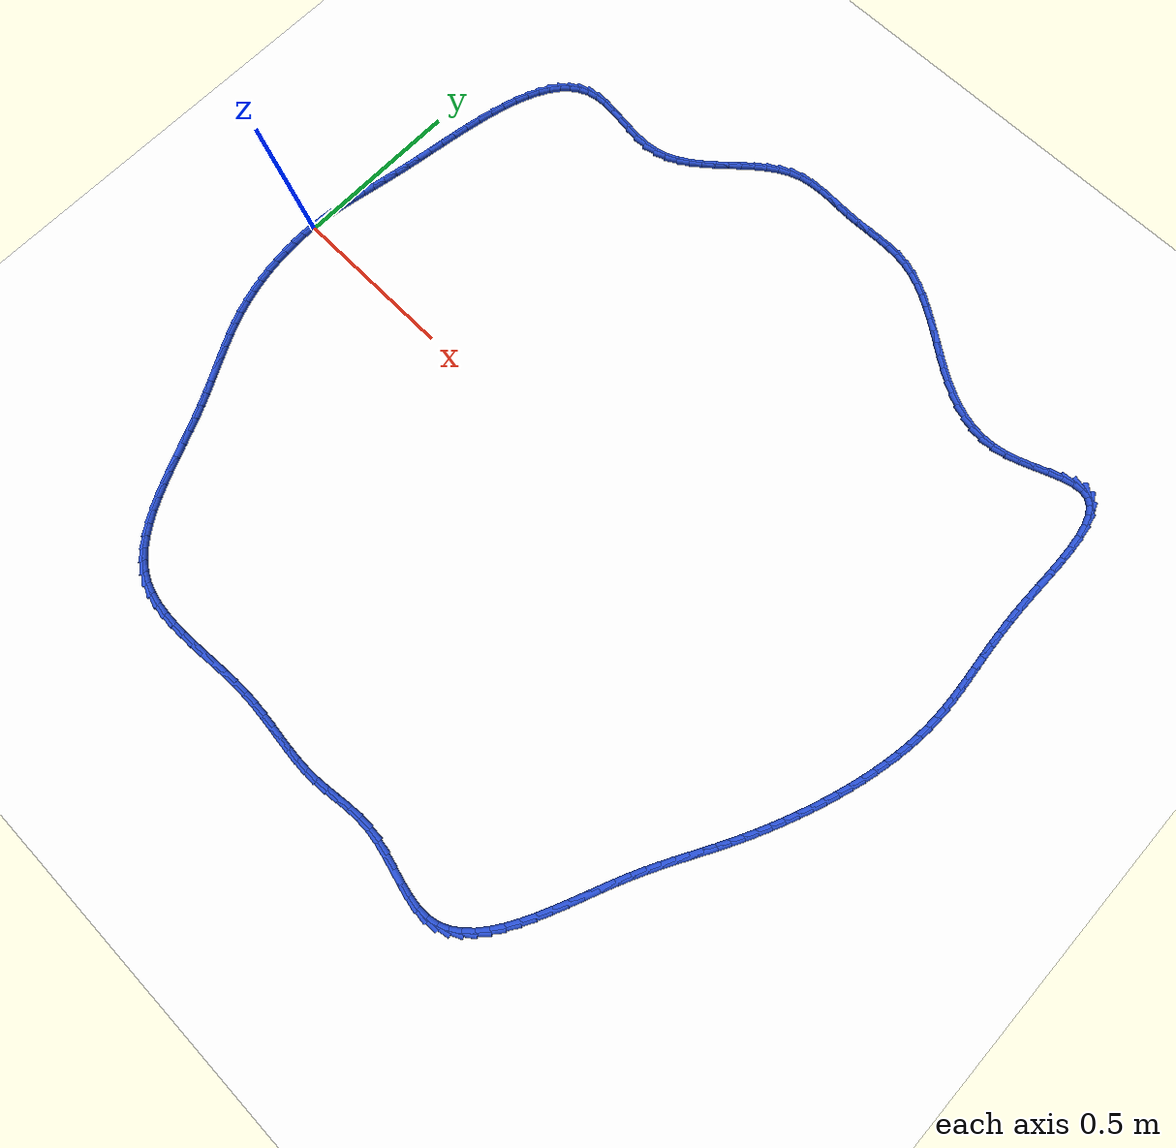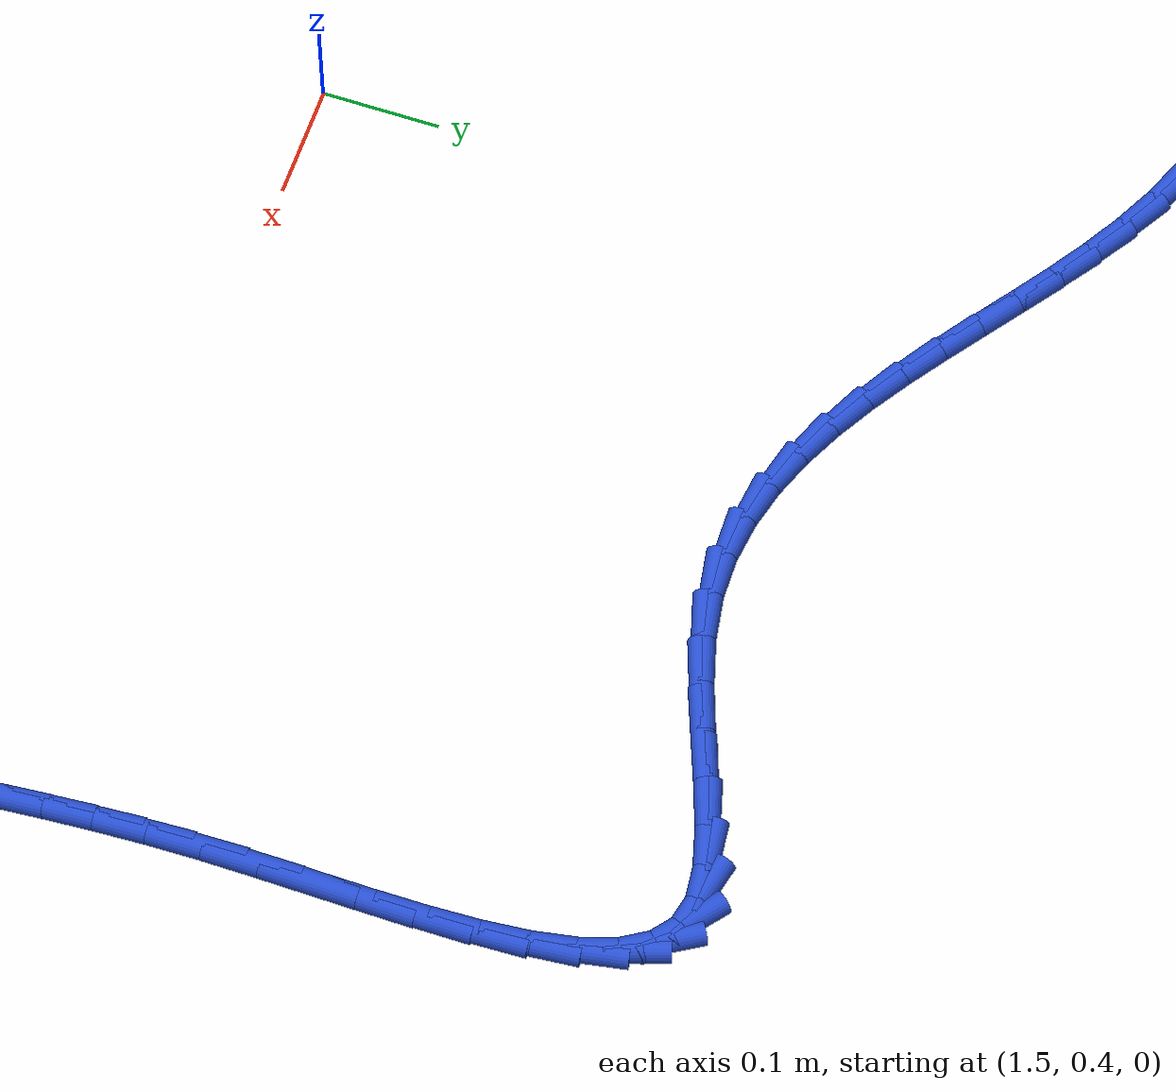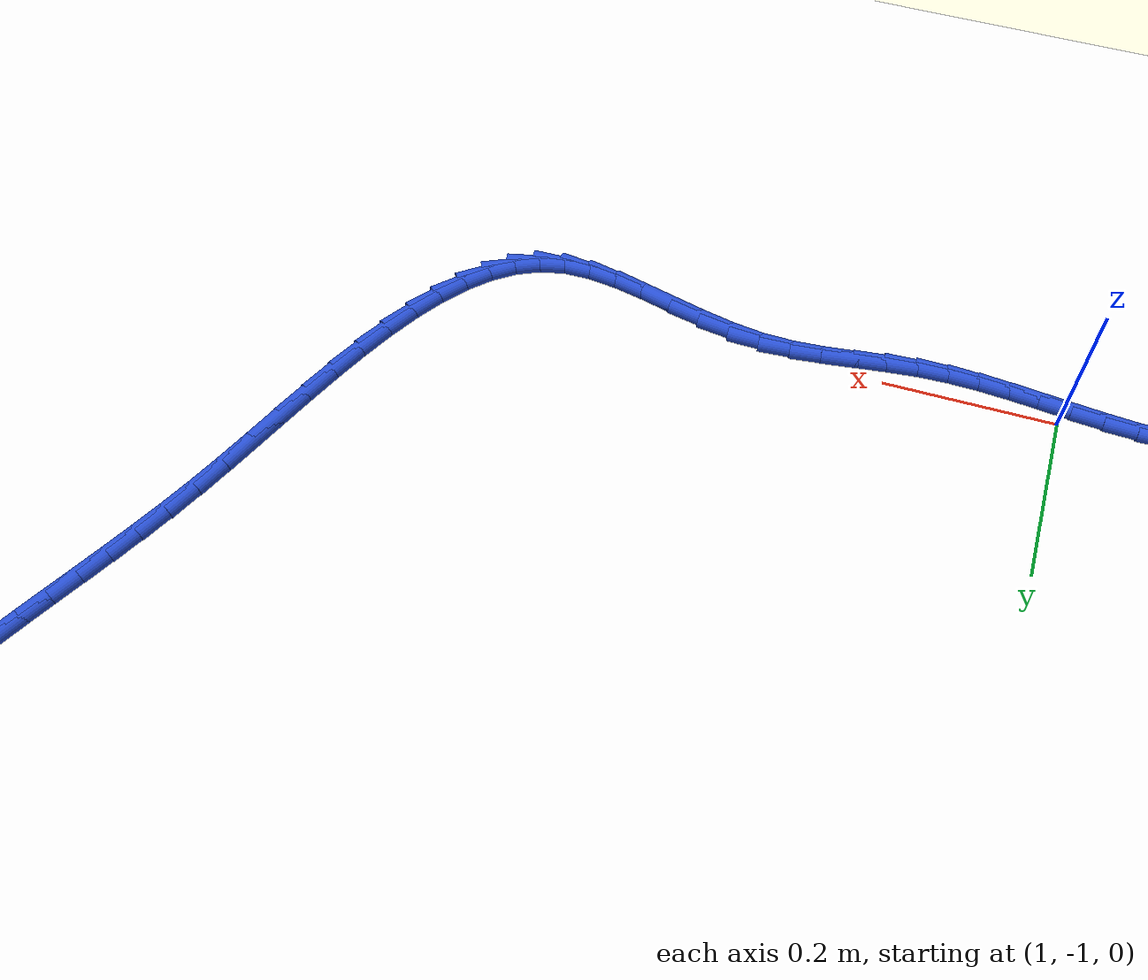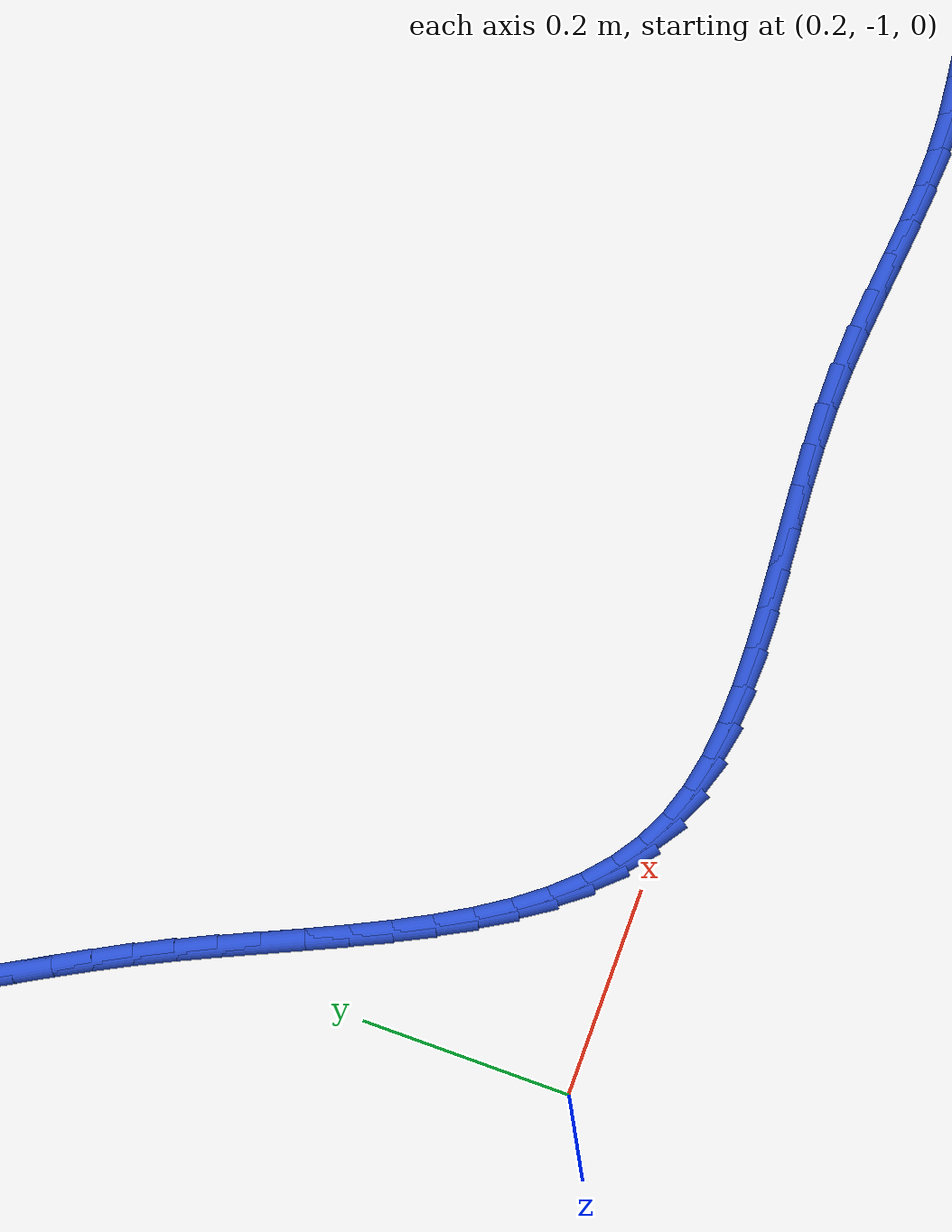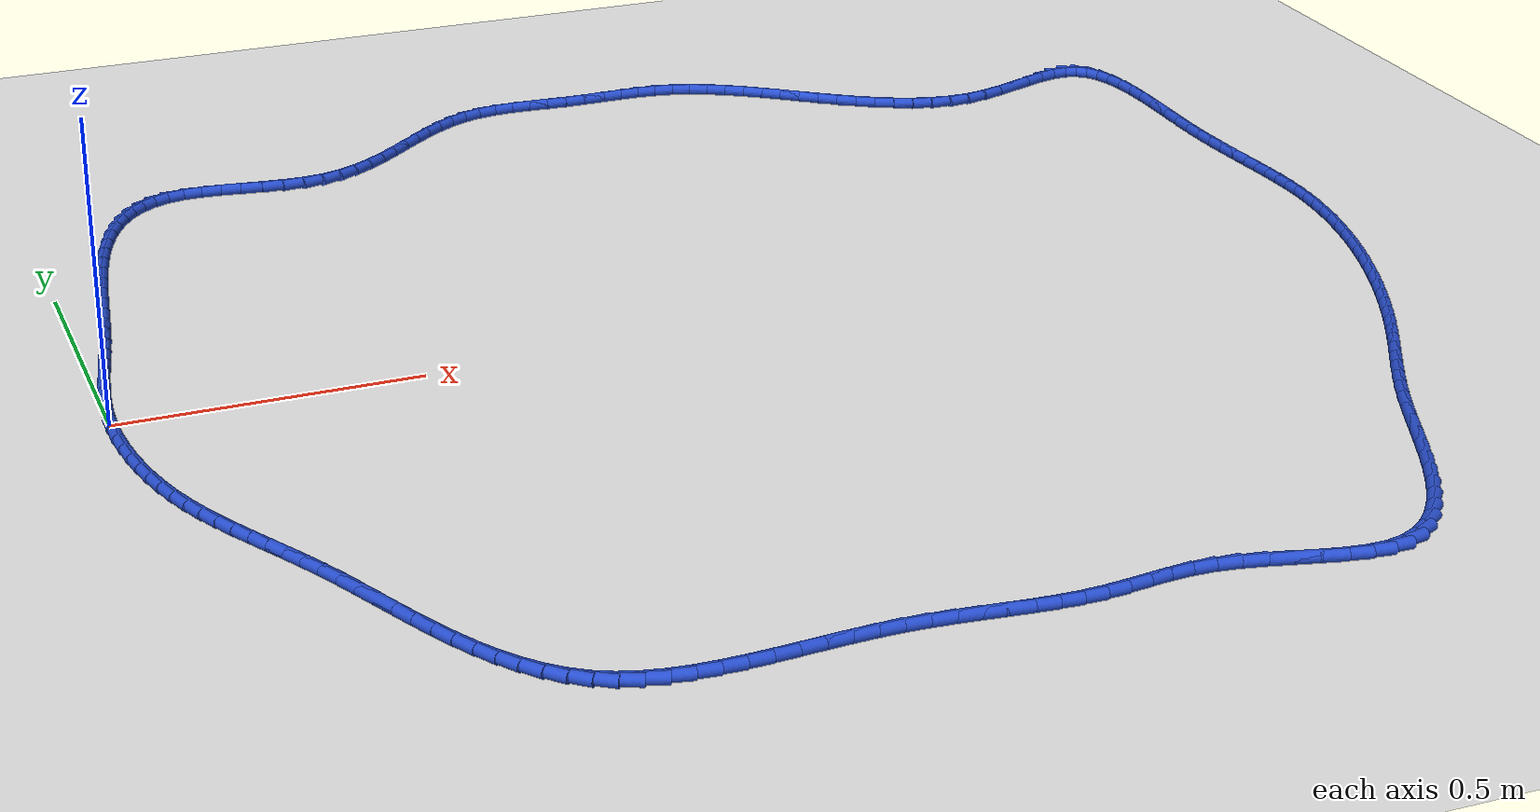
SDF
<sdf version="1.6">
 <world name="default">
  <light name="sun" type="directional">
   <pose>0 0 10 0 -0 0</pose>
   <diffuse>0.8 0.8 0.8 1</diffuse>
   <specular>0.2 0.2 0.2 1</specular>
   <attenuation>
    <range>1000</range>
    <constant>0.9</constant>
    <linear>0.01</linear>
    <quadratic>0.001</quadratic>
   </attenuation>
   <direction>-0.5 0.1 -0.9</direction>
  </light>
  <model name="ground_plane">
   <static>1</static>
   <link name="link">
    <collision name="collision">
     <geometry><plane><normal>0 0 1</normal><size>100 100</size></plane></geometry>
     <surface><friction><ode><mu>100</mu><mu2>50</mu2></ode></friction></surface>
    </collision>
    <visual name="visual">
     <cast_shadows>0</cast_shadows>
     <geometry><plane><normal>0 0 1</normal><size>100 100</size></plane></geometry>
     <material>
      <script><uri>file://media/materials/scripts/gazebo.material</uri><name>Gazebo/WhiteGlow</name></script>
     </material>
    </visual>
   </link>
  </model>
  <gravity>0 0 -9.8</gravity>
  <magnetic_field>6e-06 2.3e-05 -4.2e-05</magnetic_field>
  <atmosphere type="adiabatic"/>
  <physics name="default_physics" default="0" type="ode">
   <max_step_size>0.001</max_step_size>
   <real_time_factor>1</real_time_factor>
   <real_time_update_rate>1000</real_time_update_rate>
  </physics>
  <scene><ambient>0.4 0.4 0.4 1</ambient><background>0.7 0.7 0.7 1</background><shadows>1</shadows></scene>
  <spherical_coordinates>
   <surface_model>EARTH_WGS84</surface_model>
   <latitude_deg>0</latitude_deg>
   <longitude_deg>0</longitude_deg>
   <elevation>0</elevation>
   <heading_deg>0</heading_deg>
  </spherical_coordinates>
  <model name="line">
   <link name="link_0">
    <pose>-1.734723475976807e-18 -6.938893903907228e-18 0.01 0 1.57 1.5066727655770424</pose>
    <collision name="collision">
     <geometry><cylinder><radius>0.01</radius><length>0.08</length></cylinder></geometry>
    </collision>
    <visual name="visual">
     <material>
      <script><name>Gazebo/Blue</name><uri>file://media/materials/scripts/gazebo.material</uri></script>
     </material>
     <geometry><cylinder><radius>0.01</radius><length>0.08</length></cylinder></geometry>
    </visual>
   </link>
   <link name="link_1">
    <pose>0.0022582850308093196 0.03516942774697094 0.01 0 1.57 1.4645341288310958</pose>
    <collision name="collision">
     <geometry><cylinder><radius>0.01</radius><length>0.08</length></cylinder></geometry>
    </collision>
    <visual name="visual">
     <material>
      <script><name>Gazebo/Blue</name><uri>file://media/materials/scripts/gazebo.material</uri></script>
     </material>
     <geometry><cylinder><radius>0.01</radius><length>0.08</length></cylinder></geometry>
    </visual>
   </link>
   <link name="link_2">
    <pose>0.005962830418224047 0.06990041833474252 0.01 0 1.57 1.4299234166727632</pose>
    <collision name="collision">
     <geometry><cylinder><radius>0.01</radius><length>0.08</length></cylinder></geometry>
    </collision>
    <visual name="visual">
     <material>
      <script><name>Gazebo/Blue</name><uri>file://media/materials/scripts/gazebo.material</uri></script>
     </material>
     <geometry><cylinder><radius>0.01</radius><length>0.08</length></cylinder></geometry>
    </visual>
   </link>
   <link name="link_3">
    <pose>0.010868365868213374 0.10449217927784483 0.01 0 1.57 1.4037080650045268</pose>
    <collision name="collision">
     <geometry><cylinder><radius>0.01</radius><length>0.08</length></cylinder></geometry>
    </collision>
    <visual name="visual">
     <material>
      <script><name>Gazebo/Blue</name><uri>file://media/materials/scripts/gazebo.material</uri></script>
     </material>
     <geometry><cylinder><radius>0.01</radius><length>0.08</length></cylinder></geometry>
    </visual>
   </link>
   <link name="link_4">
    <pose>0.016729621086746478 0.139243918090808 0.01 0 1.57 1.386281005507231</pose>
    <collision name="collision">
     <geometry><cylinder><radius>0.01</radius><length>0.08</length></cylinder></geometry>
    </collision>
    <visual name="visual">
     <material>
      <script><name>Gazebo/Blue</name><uri>file://media/materials/scripts/gazebo.material</uri></script>
     </material>
     <geometry><cylinder><radius>0.01</radius><length>0.08</length></cylinder></geometry>
    </visual>
   </link>
   <link name="link_5">
    <pose>0.023301325779792527 0.17445484228816205 0.01 0 1.57 1.377600673530358</pose>
    <collision name="collision">
     <geometry><cylinder><radius>0.01</radius><length>0.08</length></cylinder></geometry>
    </collision>
    <visual name="visual">
     <material>
      <script><name>Gazebo/Blue</name><uri>file://media/materials/scripts/gazebo.material</uri></script>
     </material>
     <geometry><cylinder><radius>0.01</radius><length>0.08</length></cylinder></geometry>
    </visual>
   </link>
   <link name="link_6">
    <pose>0.030338209653320725 0.21042415938443707 0.01 0 1.57 1.3772624265243338</pose>
    <collision name="collision">
     <geometry><cylinder><radius>0.01</radius><length>0.08</length></cylinder></geometry>
    </collision>
    <visual name="visual">
     <material>
      <script><name>Gazebo/Blue</name><uri>file://media/materials/scripts/gazebo.material</uri></script>
     </material>
     <geometry><cylinder><radius>0.01</radius><length>0.08</length></cylinder></geometry>
    </visual>
   </link>
   <link name="link_7">
    <pose>0.03759500241330024 0.24745107689416318 0.01 0 1.57 1.3845806577519995</pose>
    <collision name="collision">
     <geometry><cylinder><radius>0.01</radius><length>0.08</length></cylinder></geometry>
    </collision>
    <visual name="visual">
     <material>
      <script><name>Gazebo/Blue</name><uri>file://media/materials/scripts/gazebo.material</uri></script>
     </material>
     <geometry><cylinder><radius>0.01</radius><length>0.08</length></cylinder></geometry>
    </visual>
   </link>
   <link name="link_8">
    <pose>0.04482643376570025 0.2858348023318704 0.01 0 1.57 1.398498611856168</pose>
    <collision name="collision">
     <geometry><cylinder><radius>0.01</radius><length>0.08</length></cylinder></geometry>
    </collision>
    <visual name="visual">
     <material>
      <script><name>Gazebo/Blue</name><uri>file://media/materials/scripts/gazebo.material</uri></script>
     </material>
     <geometry><cylinder><radius>0.01</radius><length>0.08</length></cylinder></geometry>
    </visual>
   </link>
   <link name="link_9">
    <pose>0.05179271196097982 0.3258655512602931 0.01 0 1.57 1.4123223762062587</pose>
    <collision name="collision">
     <geometry><cylinder><radius>0.01</radius><length>0.08</length></cylinder></geometry>
    </collision>
    <visual name="visual">
     <material>
      <script><name>Gazebo/Blue</name><uri>file://media/materials/scripts/gazebo.material</uri></script>
     </material>
     <geometry><cylinder><radius>0.01</radius><length>0.08</length></cylinder></geometry>
    </visual>
   </link>
   <link name="link_10">
    <pose>0.058448721866371886 0.3675140159167599 0.01 0 1.57 1.4192214395373546</pose>
    <collision name="collision">
     <geometry><cylinder><radius>0.01</radius><length>0.08</length></cylinder></geometry>
    </collision>
    <visual name="visual">
     <material>
      <script><name>Gazebo/Blue</name><uri>file://media/materials/scripts/gazebo.material</uri></script>
     </material>
     <geometry><cylinder><radius>0.01</radius><length>0.08</length></cylinder></geometry>
    </visual>
   </link>
   <link name="link_11">
    <pose>0.06499213408295745 0.41035240357247577 0.01 0 1.57 1.4194965987739743</pose>
    <collision name="collision">
     <geometry><cylinder><radius>0.01</radius><length>0.08</length></cylinder></geometry>
    </collision>
    <visual name="visual">
     <material>
      <script><name>Gazebo/Blue</name><uri>file://media/materials/scripts/gazebo.material</uri></script>
     </material>
     <geometry><cylinder><radius>0.01</radius><length>0.08</length></cylinder></geometry>
    </visual>
   </link>
   <link name="link_12">
    <pose>0.07163586692038312 0.4539278953880295 0.01 0 1.57 1.4134883770372186</pose>
    <collision name="collision">
     <geometry><cylinder><radius>0.01</radius><length>0.08</length></cylinder></geometry>
    </collision>
    <visual name="visual">
     <material>
      <script><name>Gazebo/Blue</name><uri>file://media/materials/scripts/gazebo.material</uri></script>
     </material>
     <geometry><cylinder><radius>0.01</radius><length>0.08</length></cylinder></geometry>
    </visual>
   </link>
   <link name="link_13">
    <pose>0.07859283868829553 0.4977876725240108 0.01 0 1.57 1.4011692170362267</pose>
    <collision name="collision">
     <geometry><cylinder><radius>0.01</radius><length>0.08</length></cylinder></geometry>
    </collision>
    <visual name="visual">
     <material>
      <script><name>Gazebo/Blue</name><uri>file://media/materials/scripts/gazebo.material</uri></script>
     </material>
     <geometry><cylinder><radius>0.01</radius><length>0.08</length></cylinder></geometry>
    </visual>
   </link>
   <link name="link_14">
    <pose>0.08607596769634124 0.5414789161410082 0.01 0 1.57 1.38216224565192</pose>
    <collision name="collision">
     <geometry><cylinder><radius>0.01</radius><length>0.08</length></cylinder></geometry>
    </collision>
    <visual name="visual">
     <material>
      <script><name>Gazebo/Blue</name><uri>file://media/materials/scripts/gazebo.material</uri></script>
     </material>
     <geometry><cylinder><radius>0.01</radius><length>0.08</length></cylinder></geometry>
    </visual>
   </link>
   <link name="link_15">
    <pose>0.0942981722541669 0.5845488073996107 0.01 0 1.57 1.3557196412298682</pose>
    <collision name="collision">
     <geometry><cylinder><radius>0.01</radius><length>0.08</length></cylinder></geometry>
    </collision>
    <visual name="visual">
     <material>
      <script><name>Gazebo/Blue</name><uri>file://media/materials/scripts/gazebo.material</uri></script>
     </material>
     <geometry><cylinder><radius>0.01</radius><length>0.08</length></cylinder></geometry>
    </visual>
   </link>
   <link name="link_16">
    <pose>0.10347237067141912 0.6265445274604079 0.01 0 1.57 1.320663005502969</pose>
    <collision name="collision">
     <geometry><cylinder><radius>0.01</radius><length>0.08</length></cylinder></geometry>
    </collision>
    <visual name="visual">
     <material>
      <script><name>Gazebo/Blue</name><uri>file://media/materials/scripts/gazebo.material</uri></script>
     </material>
     <geometry><cylinder><radius>0.01</radius><length>0.08</length></cylinder></geometry>
    </visual>
   </link>
   <link name="link_17">
    <pose>0.11381148125774447 0.6670132574839885 0.01 0 1.57 1.2752860189761903</pose>
    <collision name="collision">
     <geometry><cylinder><radius>0.01</radius><length>0.08</length></cylinder></geometry>
    </collision>
    <visual name="visual">
     <material>
      <script><name>Gazebo/Blue</name><uri>file://media/materials/scripts/gazebo.material</uri></script>
     </material>
     <geometry><cylinder><radius>0.01</radius><length>0.08</length></cylinder></geometry>
    </visual>
   </link>
   <link name="link_18">
    <pose>0.12552842232278957 0.7055021786309416 0.01 0 1.57 1.2172250605914776</pose>
    <collision name="collision">
     <geometry><cylinder><radius>0.01</radius><length>0.08</length></cylinder></geometry>
    </collision>
    <visual name="visual">
     <material>
      <script><name>Gazebo/Blue</name><uri>file://media/materials/scripts/gazebo.material</uri></script>
     </material>
     <geometry><cylinder><radius>0.01</radius><length>0.08</length></cylinder></geometry>
    </visual>
   </link>
   <link name="link_19">
    <pose>0.1388361121762011 0.7415584720618565 0.01 0 1.57 1.1433271860363068</pose>
    <collision name="collision">
     <geometry><cylinder><radius>0.01</radius><length>0.08</length></cylinder></geometry>
    </collision>
    <visual name="visual">
     <material>
      <script><name>Gazebo/Blue</name><uri>file://media/materials/scripts/gazebo.material</uri></script>
     </material>
     <geometry><cylinder><radius>0.01</radius><length>0.08</length></cylinder></geometry>
    </visual>
   </link>
   <link name="link_20">
    <pose>0.1539474691276256 0.7747293189373222 0.01 0 1.57 1.0496120278835792</pose>
    <collision name="collision">
     <geometry><cylinder><radius>0.01</radius><length>0.08</length></cylinder></geometry>
    </collision>
    <visual name="visual">
     <material>
      <script><name>Gazebo/Blue</name><uri>file://media/materials/scripts/gazebo.material</uri></script>
     </material>
     <geometry><cylinder><radius>0.01</radius><length>0.08</length></cylinder></geometry>
    </visual>
   </link>
   <link name="link_21">
    <pose>0.17107541148670966 0.8045619004179276 0.01 0 1.57 0.9315772098061283</pose>
    <collision name="collision">
     <geometry><cylinder><radius>0.01</radius><length>0.08</length></cylinder></geometry>
    </collision>
    <visual name="visual">
     <material>
      <script><name>Gazebo/Blue</name><uri>file://media/materials/scripts/gazebo.material</uri></script>
     </material>
     <geometry><cylinder><radius>0.01</radius><length>0.08</length></cylinder></geometry>
    </visual>
   </link>
   <link name="link_22">
    <pose>0.19043285756309994 0.8306033976642618 0.01 0 1.57 0.7853460059880488</pose>
    <collision name="collision">
     <geometry><cylinder><radius>0.01</radius><length>0.08</length></cylinder></geometry>
    </collision>
    <visual name="visual">
     <material>
      <script><name>Gazebo/Blue</name><uri>file://media/materials/scripts/gazebo.material</uri></script>
     </material>
     <geometry><cylinder><radius>0.01</radius><length>0.08</length></cylinder></geometry>
    </visual>
   </link>
   <link name="link_23">
    <pose>0.21223272566644308 0.8524009918369142 0.01 0 1.57 0.6102380234872056</pose>
    <collision name="collision">
     <geometry><cylinder><radius>0.01</radius><length>0.08</length></cylinder></geometry>
    </collision>
    <visual name="visual">
     <material>
      <script><name>Gazebo/Blue</name><uri>file://media/materials/scripts/gazebo.material</uri></script>
     </material>
     <geometry><cylinder><radius>0.01</radius><length>0.08</length></cylinder></geometry>
    </visual>
   </link>
   <link name="link_24">
    <pose>0.23668793410638558 0.8695018640964738 0.01 0 1.57 0.4123279480872916</pose>
    <collision name="collision">
     <geometry><cylinder><radius>0.01</radius><length>0.08</length></cylinder></geometry>
    </collision>
    <visual name="visual">
     <material>
      <script><name>Gazebo/Blue</name><uri>file://media/materials/scripts/gazebo.material</uri></script>
     </material>
     <geometry><cylinder><radius>0.01</radius><length>0.08</length></cylinder></geometry>
    </visual>
   </link>
   <link name="link_25">
    <pose>0.2640114011925742 0.8814531956035295 0.01 0 1.57 0.20617487817737432</pose>
    <collision name="collision">
     <geometry><cylinder><radius>0.01</radius><length>0.08</length></cylinder></geometry>
    </collision>
    <visual name="visual">
     <material>
      <script><name>Gazebo/Blue</name><uri>file://media/materials/scripts/gazebo.material</uri></script>
     </material>
     <geometry><cylinder><radius>0.01</radius><length>0.08</length></cylinder></geometry>
    </visual>
   </link>
   <link name="link_26">
    <pose>0.29441197622579507 0.8878113781816854 0.01 0 1.57 0.0316262559008546</pose>
    <collision name="collision">
     <geometry><cylinder><radius>0.01</radius><length>0.08</length></cylinder></geometry>
    </collision>
    <visual name="visual">
     <material>
      <script><name>Gazebo/Blue</name><uri>file://media/materials/scripts/gazebo.material</uri></script>
     </material>
     <geometry><cylinder><radius>0.01</radius><length>0.08</length></cylinder></geometry>
    </visual>
   </link>
   <link name="link_27">
    <pose>0.32777422631750425 0.8888668531664 0.01 0 1.57 -0.0755919660958112</pose>
    <collision name="collision">
     <geometry><cylinder><radius>0.01</radius><length>0.08</length></cylinder></geometry>
    </collision>
    <visual name="visual">
     <material>
      <script><name>Gazebo/Blue</name><uri>file://media/materials/scripts/gazebo.material</uri></script>
     </material>
     <geometry><cylinder><radius>0.01</radius><length>0.08</length></cylinder></geometry>
    </visual>
   </link>
   <link name="link_28">
    <pose>0.36342761662564976 0.8861665981180878 0.01 0 1.57 -0.12787966685450738</pose>
    <collision name="collision">
     <geometry><cylinder><radius>0.01</radius><length>0.08</length></cylinder></geometry>
    </collision>
    <visual name="visual">
     <material>
      <script><name>Gazebo/Blue</name><uri>file://media/materials/scripts/gazebo.material</uri></script>
     </material>
     <geometry><cylinder><radius>0.01</radius><length>0.08</length></cylinder></geometry>
    </visual>
   </link>
   <link name="link_29">
    <pose>0.40064715538259443 0.8813808600240974 0.01 0 1.57 -0.13580832637252646</pose>
    <collision name="collision">
     <geometry><cylinder><radius>0.01</radius><length>0.08</length></cylinder></geometry>
    </collision>
    <visual name="visual">
     <material>
      <script><name>Gazebo/Blue</name><uri>file://media/materials/scripts/gazebo.material</uri></script>
     </material>
     <geometry><cylinder><radius>0.01</radius><length>0.08</length></cylinder></geometry>
    </visual>
   </link>
   <link name="link_30">
    <pose>0.43870785082070085 0.8761798858717752 0.01 0 1.57 -0.10299434268488782</pose>
    <collision name="collision">
     <geometry><cylinder><radius>0.01</radius><length>0.08</length></cylinder></geometry>
    </collision>
    <visual name="visual">
     <material>
      <script><name>Gazebo/Blue</name><uri>file://media/materials/scripts/gazebo.material</uri></script>
     </material>
     <geometry><cylinder><radius>0.01</radius><length>0.08</length></cylinder></geometry>
    </visual>
   </link>
   <link name="link_31">
    <pose>0.4768847111723319 0.872233922648469 0.01 0 1.57 -0.027162834129937027</pose>
    <collision name="collision">
     <geometry><cylinder><radius>0.01</radius><length>0.08</length></cylinder></geometry>
    </collision>
    <visual name="visual">
     <material>
      <script><name>Gazebo/Blue</name><uri>file://media/materials/scripts/gazebo.material</uri></script>
     </material>
     <geometry><cylinder><radius>0.01</radius><length>0.08</length></cylinder></geometry>
    </visual>
   </link>
   <link name="link_32">
    <pose>0.51445274466985 0.8712132173415266 0.01 0 1.57 0.09833940239529257</pose>
    <collision name="collision">
     <geometry><cylinder><radius>0.01</radius><length>0.08</length></cylinder></geometry>
    </collision>
    <visual name="visual">
     <material>
      <script><name>Gazebo/Blue</name><uri>file://media/materials/scripts/gazebo.material</uri></script>
     </material>
     <geometry><cylinder><radius>0.01</radius><length>0.08</length></cylinder></geometry>
    </visual>
   </link>
   <link name="link_33">
    <pose>0.550686966168279 0.8747879999423103 0.01 0 1.57 0.2656169951487791</pose>
    <collision name="collision">
     <geometry><cylinder><radius>0.01</radius><length>0.08</length></cylinder></geometry>
    </collision>
    <visual name="visual">
     <material>
      <script><name>Gazebo/Blue</name><uri>file://media/materials/scripts/gazebo.material</uri></script>
     </material>
     <geometry><cylinder><radius>0.01</radius><length>0.08</length></cylinder></geometry>
    </visual>
   </link>
   <link name="link_34">
    <pose>0.5850537825099087 0.8841373239774409 0.01 0 1.57 0.4185360274429377</pose>
    <collision name="collision">
     <geometry><cylinder><radius>0.01</radius><length>0.08</length></cylinder></geometry>
    </collision>
    <visual name="visual">
     <material>
      <script><name>Gazebo/Blue</name><uri>file://media/materials/scripts/gazebo.material</uri></script>
     </material>
     <geometry><cylinder><radius>0.01</radius><length>0.08</length></cylinder></geometry>
    </visual>
   </link>
   <link name="link_35">
    <pose>0.6177116788272122 0.8986641363937734 0.01 0 1.57 0.5391866174887862</pose>
    <collision name="collision">
     <geometry><cylinder><radius>0.01</radius><length>0.08</length></cylinder></geometry>
    </collision>
    <visual name="visual">
     <material>
      <script><name>Gazebo/Blue</name><uri>file://media/materials/scripts/gazebo.material</uri></script>
     </material>
     <geometry><cylinder><radius>0.01</radius><length>0.08</length></cylinder></geometry>
    </visual>
   </link>
   <link name="link_36">
    <pose>0.6489755205719054 0.9173700594356077 0.01 0 1.57 0.6273686181092974</pose>
    <collision name="collision">
     <geometry><cylinder><radius>0.01</radius><length>0.08</length></cylinder></geometry>
    </collision>
    <visual name="visual">
     <material>
      <script><name>Gazebo/Blue</name><uri>file://media/materials/scripts/gazebo.material</uri></script>
     </material>
     <geometry><cylinder><radius>0.01</radius><length>0.08</length></cylinder></geometry>
    </visual>
   </link>
   <link name="link_37">
    <pose>0.6791601731957047 0.9392567153472446 0.01 0 1.57 0.6856853840362732</pose>
    <collision name="collision">
     <geometry><cylinder><radius>0.01</radius><length>0.08</length></cylinder></geometry>
    </collision>
    <visual name="visual">
     <material>
      <script><name>Gazebo/Blue</name><uri>file://media/materials/scripts/gazebo.material</uri></script>
     </material>
     <geometry><cylinder><radius>0.01</radius><length>0.08</length></cylinder></geometry>
    </visual>
   </link>
   <link name="link_38">
    <pose>0.7085805021503251 0.9633257263729841 0.01 0 1.57 0.7169398758496753</pose>
    <collision name="collision">
     <geometry><cylinder><radius>0.01</radius><length>0.08</length></cylinder></geometry>
    </collision>
    <visual name="visual">
     <material>
      <script><name>Gazebo/Blue</name><uri>file://media/materials/scripts/gazebo.material</uri></script>
     </material>
     <geometry><cylinder><radius>0.01</radius><length>0.08</length></cylinder></geometry>
    </visual>
   </link>
   <link name="link_39">
    <pose>0.7375513728874832 0.988578714757127 0.01 0 1.57 0.722878212950674</pose>
    <collision name="collision">
     <geometry><cylinder><radius>0.01</radius><length>0.08</length></cylinder></geometry>
    </collision>
    <visual name="visual">
     <material>
      <script><name>Gazebo/Blue</name><uri>file://media/materials/scripts/gazebo.material</uri></script>
     </material>
     <geometry><cylinder><radius>0.01</radius><length>0.08</length></cylinder></geometry>
    </visual>
   </link>
   <link name="link_40">
    <pose>0.766387650858894 1.0140173027439734 0.01 0 1.57 0.7037281107930893</pose>
    <collision name="collision">
     <geometry><cylinder><radius>0.01</radius><length>0.08</length></cylinder></geometry>
    </collision>
    <visual name="visual">
     <material>
      <script><name>Gazebo/Blue</name><uri>file://media/materials/scripts/gazebo.material</uri></script>
     </material>
     <geometry><cylinder><radius>0.01</radius><length>0.08</length></cylinder></geometry>
    </visual>
   </link>
   <link name="link_41">
    <pose>0.7954042015162741 1.038643112577824 0.01 0 1.57 0.6581042791591748</pose>
    <collision name="collision">
     <geometry><cylinder><radius>0.01</radius><length>0.08</length></cylinder></geometry>
    </collision>
    <visual name="visual">
     <material>
      <script><name>Gazebo/Blue</name><uri>file://media/materials/scripts/gazebo.material</uri></script>
     </material>
     <geometry><cylinder><radius>0.01</radius><length>0.08</length></cylinder></geometry>
    </visual>
   </link>
   <link name="link_42">
    <pose>0.8249158903113385 1.0614577665029783 0.01 0 1.57 0.5832076606168878</pose>
    <collision name="collision">
     <geometry><cylinder><radius>0.01</radius><length>0.08</length></cylinder></geometry>
    </collision>
    <visual name="visual">
     <material>
      <script><name>Gazebo/Blue</name><uri>file://media/materials/scripts/gazebo.material</uri></script>
     </material>
     <geometry><cylinder><radius>0.01</radius><length>0.08</length></cylinder></geometry>
    </visual>
   </link>
   <link name="link_43">
    <pose>0.8552375826958036 1.0814628867637375 0.01 0 1.57 0.47563151221520694</pose>
    <collision name="collision">
     <geometry><cylinder><radius>0.01</radius><length>0.08</length></cylinder></geometry>
    </collision>
    <visual name="visual">
     <material>
      <script><name>Gazebo/Blue</name><uri>file://media/materials/scripts/gazebo.material</uri></script>
     </material>
     <geometry><cylinder><radius>0.01</radius><length>0.08</length></cylinder></geometry>
    </visual>
   </link>
   <link name="link_44">
    <pose>0.8866841441213851 1.0976600956044016 0.01 0 1.57 0.3334770963094323</pose>
    <collision name="collision">
     <geometry><cylinder><radius>0.01</radius><length>0.08</length></cylinder></geometry>
    </collision>
    <visual name="visual">
     <material>
      <script><name>Gazebo/Blue</name><uri>file://media/materials/scripts/gazebo.material</uri></script>
     </material>
     <geometry><cylinder><radius>0.01</radius><length>0.08</length></cylinder></geometry>
    </visual>
   </link>
   <link name="link_45">
    <pose>0.919570093252505 1.1090522670865648 0.01 0 1.57 0.17741898869911157</pose>
    <collision name="collision">
     <geometry><cylinder><radius>0.01</radius><length>0.08</length></cylinder></geometry>
    </collision>
    <visual name="visual">
     <material>
      <script><name>Gazebo/Blue</name><uri>file://media/materials/scripts/gazebo.material</uri></script>
     </material>
     <geometry><cylinder><radius>0.01</radius><length>0.08</length></cylinder></geometry>
    </visual>
   </link>
   <link name="link_46">
    <pose>0.9540460382133769 1.1152339522230308 0.01 0 1.57 0.058628369075735126</pose>
    <collision name="collision">
     <geometry><cylinder><radius>0.01</radius><length>0.08</length></cylinder></geometry>
    </collision>
    <visual name="visual">
     <material>
      <script><name>Gazebo/Blue</name><uri>file://media/materials/scripts/gazebo.material</uri></script>
     </material>
     <geometry><cylinder><radius>0.01</radius><length>0.08</length></cylinder></geometry>
    </visual>
   </link>
   <link name="link_47">
    <pose>0.989837338553318 1.1173347453495102 0.01 0 1.57 -0.016449524241036087</pose>
    <collision name="collision">
     <geometry><cylinder><radius>0.01</radius><length>0.08</length></cylinder></geometry>
    </collision>
    <visual name="visual">
     <material>
      <script><name>Gazebo/Blue</name><uri>file://media/materials/scripts/gazebo.material</uri></script>
     </material>
     <geometry><cylinder><radius>0.01</radius><length>0.08</length></cylinder></geometry>
    </visual>
   </link>
   <link name="link_48">
    <pose>1.0266012881241353 1.1167299413181926 0.01 0 1.57 -0.05170314118292978</pose>
    <collision name="collision">
     <geometry><cylinder><radius>0.01</radius><length>0.08</length></cylinder></geometry>
    </collision>
    <visual name="visual">
     <material>
      <script><name>Gazebo/Blue</name><uri>file://media/materials/scripts/gazebo.material</uri></script>
     </material>
     <geometry><cylinder><radius>0.01</radius><length>0.08</length></cylinder></geometry>
    </visual>
   </link>
   <link name="link_49">
    <pose>1.0639951807776362 1.1147948349812677 0.01 0 1.57 -0.05011874539832529</pose>
    <collision name="collision">
     <geometry><cylinder><radius>0.01</radius><length>0.08</length></cylinder></geometry>
    </collision>
    <visual name="visual">
     <material>
      <script><name>Gazebo/Blue</name><uri>file://media/materials/scripts/gazebo.material</uri></script>
     </material>
     <geometry><cylinder><radius>0.01</radius><length>0.08</length></cylinder></geometry>
    </visual>
   </link>
   <link name="link_50">
    <pose>1.1016763103656264 1.1129047211909244 0.01 0 1.57 -0.015018872214611156</pose>
    <collision name="collision">
     <geometry><cylinder><radius>0.01</radius><length>0.08</length></cylinder></geometry>
    </collision>
    <visual name="visual">
     <material>
      <script><name>Gazebo/Blue</name><uri>file://media/materials/scripts/gazebo.material</uri></script>
     </material>
     <geometry><cylinder><radius>0.01</radius><length>0.08</length></cylinder></geometry>
    </visual>
   </link>
   <link name="link_51">
    <pose>1.1393094751861828 1.112339470996307 0.01 0 1.57 0.017598746608704093</pose>
    <collision name="collision">
     <geometry><cylinder><radius>0.01</radius><length>0.08</length></cylinder></geometry>
    </collision>
    <visual name="visual">
     <material>
      <script><name>Gazebo/Blue</name><uri>file://media/materials/scripts/gazebo.material</uri></script>
     </material>
     <geometry><cylinder><radius>0.01</radius><length>0.08</length></cylinder></geometry>
    </visual>
   </link>
   <link name="link_52">
    <pose>1.1766681547460989 1.1129970048158084 0.01 0 1.57 0.019959532412336663</pose>
    <collision name="collision">
     <geometry><cylinder><radius>0.01</radius><length>0.08</length></cylinder></geometry>
    </collision>
    <visual name="visual">
     <material>
      <script><name>Gazebo/Blue</name><uri>file://media/materials/scripts/gazebo.material</uri></script>
     </material>
     <geometry><cylinder><radius>0.01</radius><length>0.08</length></cylinder></geometry>
    </visual>
   </link>
   <link name="link_53">
    <pose>1.2136076840441103 1.1137343984724122 0.01 0 1.57 -0.009652594679860653</pose>
    <collision name="collision">
     <geometry><cylinder><radius>0.01</radius><length>0.08</length></cylinder></geometry>
    </collision>
    <visual name="visual">
     <material>
      <script><name>Gazebo/Blue</name><uri>file://media/materials/scripts/gazebo.material</uri></script>
     </material>
     <geometry><cylinder><radius>0.01</radius><length>0.08</length></cylinder></geometry>
    </visual>
   </link>
   <link name="link_54">
    <pose>1.2499854018787886 1.1133832482008486 0.01 0 1.57 -0.07298090989414706</pose>
    <collision name="collision">
     <geometry><cylinder><radius>0.01</radius><length>0.08</length></cylinder></geometry>
    </collision>
    <visual name="visual">
     <material>
      <script><name>Gazebo/Blue</name><uri>file://media/materials/scripts/gazebo.material</uri></script>
     </material>
     <geometry><cylinder><radius>0.01</radius><length>0.08</length></cylinder></geometry>
    </visual>
   </link>
   <link name="link_55">
    <pose>1.2856586470487057 1.1107751502358494 0.01 0 1.57 -0.17152839287614283</pose>
    <collision name="collision">
     <geometry><cylinder><radius>0.01</radius><length>0.08</length></cylinder></geometry>
    </collision>
    <visual name="visual">
     <material>
      <script><name>Gazebo/Blue</name><uri>file://media/materials/scripts/gazebo.material</uri></script>
     </material>
     <geometry><cylinder><radius>0.01</radius><length>0.08</length></cylinder></geometry>
    </visual>
   </link>
   <link name="link_56">
    <pose>1.3204848357874224 1.1047421864044682 0.01 0 1.57 -0.29247017391245833</pose>
    <collision name="collision">
     <geometry><cylinder><radius>0.01</radius><length>0.08</length></cylinder></geometry>
    </collision>
    <visual name="visual">
     <material>
      <script><name>Gazebo/Blue</name><uri>file://media/materials/scripts/gazebo.material</uri></script>
     </material>
     <geometry><cylinder><radius>0.01</radius><length>0.08</length></cylinder></geometry>
    </visual>
   </link>
   <link name="link_57">
    <pose>1.3543879381617003 1.09453379548062 0.01 0 1.57 -0.3990852005120483</pose>
    <collision name="collision">
     <geometry><cylinder><radius>0.01</radius><length>0.08</length></cylinder></geometry>
    </collision>
    <visual name="visual">
     <material>
      <script><name>Gazebo/Blue</name><uri>file://media/materials/scripts/gazebo.material</uri></script>
     </material>
     <geometry><cylinder><radius>0.01</radius><length>0.08</length></cylinder></geometry>
    </visual>
   </link>
   <link name="link_58">
    <pose>1.3874799302251335 1.0805783957332036 0.01 0 1.57 -0.4845035469702688</pose>
    <collision name="collision">
     <geometry><cylinder><radius>0.01</radius><length>0.08</length></cylinder></geometry>
    </collision>
    <visual name="visual">
     <material>
      <script><name>Gazebo/Blue</name><uri>file://media/materials/scripts/gazebo.material</uri></script>
     </material>
     <geometry><cylinder><radius>0.01</radius><length>0.08</length></cylinder></geometry>
    </visual>
   </link>
   <link name="link_59">
    <pose>1.419905750753244 1.063511113599853 0.01 0 1.57 -0.5496164934349463</pose>
    <collision name="collision">
     <geometry><cylinder><radius>0.01</radius><length>0.08</length></cylinder></geometry>
    </collision>
    <visual name="visual">
     <material>
      <script><name>Gazebo/Blue</name><uri>file://media/materials/scripts/gazebo.material</uri></script>
     </material>
     <geometry><cylinder><radius>0.01</radius><length>0.08</length></cylinder></geometry>
    </visual>
   </link>
   <link name="link_60">
    <pose>1.4518103385215522 1.0439670755182027 0.01 0 1.57 -0.5960138293594356</pose>
    <collision name="collision">
     <geometry><cylinder><radius>0.01</radius><length>0.08</length></cylinder></geometry>
    </collision>
    <visual name="visual">
     <material>
      <script><name>Gazebo/Blue</name><uri>file://media/materials/scripts/gazebo.material</uri></script>
     </material>
     <geometry><cylinder><radius>0.01</radius><length>0.08</length></cylinder></geometry>
    </visual>
   </link>
   <link name="link_61">
    <pose>1.483338632305579 1.0225814079258868 0.01 0 1.57 -0.6252503618484937</pose>
    <collision name="collision">
     <geometry><cylinder><radius>0.01</radius><length>0.08</length></cylinder></geometry>
    </collision>
    <visual name="visual">
     <material>
      <script><name>Gazebo/Blue</name><uri>file://media/materials/scripts/gazebo.material</uri></script>
     </material>
     <geometry><cylinder><radius>0.01</radius><length>0.08</length></cylinder></geometry>
    </visual>
   </link>
   <link name="link_62">
    <pose>1.5146355708808465 0.9999892372605405 0.01 0 1.57 -0.6384717502287445</pose>
    <collision name="collision">
     <geometry><cylinder><radius>0.01</radius><length>0.08</length></cylinder></geometry>
    </collision>
    <visual name="visual">
     <material>
      <script><name>Gazebo/Blue</name><uri>file://media/materials/scripts/gazebo.material</uri></script>
     </material>
     <geometry><cylinder><radius>0.01</radius><length>0.08</length></cylinder></geometry>
    </visual>
   </link>
   <link name="link_63">
    <pose>1.5458460930228746 0.976825689959798 0.01 0 1.57 -0.6362578177100335</pose>
    <collision name="collision">
     <geometry><cylinder><radius>0.01</radius><length>0.08</length></cylinder></geometry>
    </collision>
    <visual name="visual">
     <material>
      <script><name>Gazebo/Blue</name><uri>file://media/materials/scripts/gazebo.material</uri></script>
     </material>
     <geometry><cylinder><radius>0.01</radius><length>0.08</length></cylinder></geometry>
    </visual>
   </link>
   <link name="link_64">
    <pose>1.5771151375071846 0.9537258924612937 0.01 0 1.57 -0.6185761234872691</pose>
    <collision name="collision">
     <geometry><cylinder><radius>0.01</radius><length>0.08</length></cylinder></geometry>
    </collision>
    <visual name="visual">
     <material>
      <script><name>Gazebo/Blue</name><uri>file://media/materials/scripts/gazebo.material</uri></script>
     </material>
     <geometry><cylinder><radius>0.01</radius><length>0.08</length></cylinder></geometry>
    </visual>
   </link>
   <link name="link_65">
    <pose>1.6085876431092976 0.931324971202662 0.01 0 1.57 -0.5847971908737696</pose>
    <collision name="collision">
     <geometry><cylinder><radius>0.01</radius><length>0.08</length></cylinder></geometry>
    </collision>
    <visual name="visual">
     <material>
      <script><name>Gazebo/Blue</name><uri>file://media/materials/scripts/gazebo.material</uri></script>
     </material>
     <geometry><cylinder><radius>0.01</radius><length>0.08</length></cylinder></geometry>
    </visual>
   </link>
   <link name="link_66">
    <pose>1.6404085486047353 0.9102580526215378 0.01 0 1.57 -0.5337772024568379</pose>
    <collision name="collision">
     <geometry><cylinder><radius>0.01</radius><length>0.08</length></cylinder></geometry>
    </collision>
    <visual name="visual">
     <material>
      <script><name>Gazebo/Blue</name><uri>file://media/materials/scripts/gazebo.material</uri></script>
     </material>
     <geometry><cylinder><radius>0.01</radius><length>0.08</length></cylinder></geometry>
    </visual>
   </link>
   <link name="link_67">
    <pose>1.6727227927690174 0.8911602631555552 0.01 0 1.57 -0.46406686643149403</pose>
    <collision name="collision">
     <geometry><cylinder><radius>0.01</radius><length>0.08</length></cylinder></geometry>
    </collision>
    <visual name="visual">
     <material>
      <script><name>Gazebo/Blue</name><uri>file://media/materials/scripts/gazebo.material</uri></script>
     </material>
     <geometry><cylinder><radius>0.01</radius><length>0.08</length></cylinder></geometry>
    </visual>
   </link>
   <link name="link_68">
    <pose>1.705675314377666 0.8746667292423488 0.01 0 1.57 -0.37435483556211635</pose>
    <collision name="collision">
     <geometry><cylinder><radius>0.01</radius><length>0.08</length></cylinder></geometry>
    </collision>
    <visual name="visual">
     <material>
      <script><name>Gazebo/Blue</name><uri>file://media/materials/scripts/gazebo.material</uri></script>
     </material>
     <geometry><cylinder><radius>0.01</radius><length>0.08</length></cylinder></geometry>
    </visual>
   </link>
   <link name="link_69">
    <pose>1.7394110522062012 0.8614125773195529 0.01 0 1.57 -0.2642600711767</pose>
    <collision name="collision">
     <geometry><cylinder><radius>0.01</radius><length>0.08</length></cylinder></geometry>
    </collision>
    <visual name="visual">
     <material>
      <script><name>Gazebo/Blue</name><uri>file://media/materials/scripts/gazebo.material</uri></script>
     </material>
     <geometry><cylinder><radius>0.01</radius><length>0.08</length></cylinder></geometry>
    </visual>
   </link>
   <link name="link_70">
    <pose>1.7740749450301445 0.8520329338248022 0.01 0 1.57 -0.1354393425472786</pose>
    <collision name="collision">
     <geometry><cylinder><radius>0.01</radius><length>0.08</length></cylinder></geometry>
    </collision>
    <visual name="visual">
     <material>
      <script><name>Gazebo/Blue</name><uri>file://media/materials/scripts/gazebo.material</uri></script>
     </material>
     <geometry><cylinder><radius>0.01</radius><length>0.08</length></cylinder></geometry>
    </visual>
   </link>
   <link name="link_71">
    <pose>1.8098119316250165 0.8471629251957311 0.01 0 1.57 0.007434649430058432</pose>
    <collision name="collision">
     <geometry><cylinder><radius>0.01</radius><length>0.08</length></cylinder></geometry>
    </collision>
    <visual name="visual">
     <material>
      <script><name>Gazebo/Blue</name><uri>file://media/materials/scripts/gazebo.material</uri></script>
     </material>
     <geometry><cylinder><radius>0.01</radius><length>0.08</length></cylinder></geometry>
    </visual>
   </link>
   <link name="link_72">
    <pose>1.8467669507663393 0.8474376778699741 0.01 0 1.57 0.1558963586968412</pose>
    <collision name="collision">
     <geometry><cylinder><radius>0.01</radius><length>0.08</length></cylinder></geometry>
    </collision>
    <visual name="visual">
     <material>
      <script><name>Gazebo/Blue</name><uri>file://media/materials/scripts/gazebo.material</uri></script>
     </material>
     <geometry><cylinder><radius>0.01</radius><length>0.08</length></cylinder></geometry>
    </visual>
   </link>
   <link name="link_73">
    <pose>1.8850712559053295 0.8534580310045085 0.01 0 1.57 0.2759679046431737</pose>
    <collision name="collision">
     <geometry><cylinder><radius>0.01</radius><length>0.08</length></cylinder></geometry>
    </collision>
    <visual name="visual">
     <material>
      <script><name>Gazebo/Blue</name><uri>file://media/materials/scripts/gazebo.material</uri></script>
     </material>
     <geometry><cylinder><radius>0.01</radius><length>0.08</length></cylinder></geometry>
    </visual>
   </link>
   <link name="link_74">
    <pose>1.9243611119427555 0.8645846769410488 0.01 0 1.57 0.3430791928492612</pose>
    <collision name="collision">
     <geometry><cylinder><radius>0.01</radius><length>0.08</length></cylinder></geometry>
    </collision>
    <visual name="visual">
     <material>
      <script><name>Gazebo/Blue</name><uri>file://media/materials/scripts/gazebo.material</uri></script>
     </material>
     <geometry><cylinder><radius>0.01</radius><length>0.08</length></cylinder></geometry>
    </visual>
   </link>
   <link name="link_75">
    <pose>1.9636504133811656 0.8786190180810297 0.01 0 1.57 0.3655269714927042</pose>
    <collision name="collision">
     <geometry><cylinder><radius>0.01</radius><length>0.08</length></cylinder></geometry>
    </collision>
    <visual name="visual">
     <material>
      <script><name>Gazebo/Blue</name><uri>file://media/materials/scripts/gazebo.material</uri></script>
     </material>
     <geometry><cylinder><radius>0.01</radius><length>0.08</length></cylinder></geometry>
    </visual>
   </link>
   <link name="link_76">
    <pose>2.0019134734861965 0.893263289794938 0.01 0 1.57 0.34360894084114635</pose>
    <collision name="collision">
     <geometry><cylinder><radius>0.01</radius><length>0.08</length></cylinder></geometry>
    </collision>
    <visual name="visual">
     <material>
      <script><name>Gazebo/Blue</name><uri>file://media/materials/scripts/gazebo.material</uri></script>
     </material>
     <geometry><cylinder><radius>0.01</radius><length>0.08</length></cylinder></geometry>
    </visual>
   </link>
   <link name="link_77">
    <pose>2.038124605523482 0.9062197274532594 0.01 0 1.57 0.2644090322370107</pose>
    <collision name="collision">
     <geometry><cylinder><radius>0.01</radius><length>0.08</length></cylinder></geometry>
    </collision>
    <visual name="visual">
     <material>
      <script><name>Gazebo/Blue</name><uri>file://media/materials/scripts/gazebo.material</uri></script>
     </material>
     <geometry><cylinder><radius>0.01</radius><length>0.08</length></cylinder></geometry>
    </visual>
   </link>
   <link name="link_78">
    <pose>2.0712581227586577 0.9151905664264811 0.01 0 1.57 0.09231200915744743</pose>
    <collision name="collision">
     <geometry><cylinder><radius>0.01</radius><length>0.08</length></cylinder></geometry>
    </collision>
    <visual name="visual">
     <material>
      <script><name>Gazebo/Blue</name><uri>file://media/materials/scripts/gazebo.material</uri></script>
     </material>
     <geometry><cylinder><radius>0.01</radius><length>0.08</length></cylinder></geometry>
    </visual>
   </link>
   <link name="link_79">
    <pose>2.10028833845736 0.9178780420850896 0.01 0 1.57 -0.23932354117319063</pose>
    <collision name="collision">
     <geometry><cylinder><radius>0.01</radius><length>0.08</length></cylinder></geometry>
    </collision>
    <visual name="visual">
     <material>
      <script><name>Gazebo/Blue</name><uri>file://media/materials/scripts/gazebo.material</uri></script>
     </material>
     <geometry><cylinder><radius>0.01</radius><length>0.08</length></cylinder></geometry>
    </visual>
   </link>
   <link name="link_80">
    <pose>2.124216322068684 0.9120396176287598 0.01 0 1.57 -0.6800317864324226</pose>
    <collision name="collision">
     <geometry><cylinder><radius>0.01</radius><length>0.08</length></cylinder></geometry>
    </collision>
    <visual name="visual">
     <material>
      <script><name>Gazebo/Blue</name><uri>file://media/materials/scripts/gazebo.material</uri></script>
     </material>
     <geometry><cylinder><radius>0.01</radius><length>0.08</length></cylinder></geometry>
    </visual>
   </link>
   <link name="link_81">
    <pose>2.1428054797203564 0.8970063065332665 0.01 0 1.57 -1.030774208055247</pose>
    <collision name="collision">
     <geometry><cylinder><radius>0.01</radius><length>0.08</length></cylinder></geometry>
    </collision>
    <visual name="visual">
     <material>
      <script><name>Gazebo/Blue</name><uri>file://media/materials/scripts/gazebo.material</uri></script>
     </material>
     <geometry><cylinder><radius>0.01</radius><length>0.08</length></cylinder></geometry>
    </visual>
   </link>
   <link name="link_82">
    <pose>2.156673405549451 0.8738722642241663 0.01 0 1.57 -1.2552372053446037</pose>
    <collision name="collision">
     <geometry><cylinder><radius>0.01</radius><length>0.08</length></cylinder></geometry>
    </collision>
    <visual name="visual">
     <material>
      <script><name>Gazebo/Blue</name><uri>file://media/materials/scripts/gazebo.material</uri></script>
     </material>
     <geometry><cylinder><radius>0.01</radius><length>0.08</length></cylinder></geometry>
    </visual>
   </link>
   <link name="link_83">
    <pose>2.166482894703999 0.8438249461941214 0.01 0 1.57 -1.3933889796489545</pose>
    <collision name="collision">
     <geometry><cylinder><radius>0.01</radius><length>0.08</length></cylinder></geometry>
    </collision>
    <visual name="visual">
     <material>
      <script><name>Gazebo/Blue</name><uri>file://media/materials/scripts/gazebo.material</uri></script>
     </material>
     <geometry><cylinder><radius>0.01</radius><length>0.08</length></cylinder></geometry>
    </visual>
   </link>
   <link name="link_84">
    <pose>2.172896742332034 0.8080518079357941 0.01 0 1.57 -1.4797349461551859</pose>
    <collision name="collision">
     <geometry><cylinder><radius>0.01</radius><length>0.08</length></cylinder></geometry>
    </collision>
    <visual name="visual">
     <material>
      <script><name>Gazebo/Blue</name><uri>file://media/materials/scripts/gazebo.material</uri></script>
     </material>
     <geometry><cylinder><radius>0.01</radius><length>0.08</length></cylinder></geometry>
    </visual>
   </link>
   <link name="link_85">
    <pose>2.1765777435815865 0.7677403049418462 0.01 0 1.57 -1.5339174750240627</pose>
    <collision name="collision">
     <geometry><cylinder><radius>0.01</radius><length>0.08</length></cylinder></geometry>
    </collision>
    <visual name="visual">
     <material>
      <script><name>Gazebo/Blue</name><uri>file://media/materials/scripts/gazebo.material</uri></script>
     </material>
     <geometry><cylinder><radius>0.01</radius><length>0.08</length></cylinder></geometry>
    </visual>
   </link>
   <link name="link_86">
    <pose>2.17818869360069 0.72407789270494 0.01 0 1.57 -1.5663514005330446</pose>
    <collision name="collision">
     <geometry><cylinder><radius>0.01</radius><length>0.08</length></cylinder></geometry>
    </collision>
    <visual name="visual">
     <material>
      <script><name>Gazebo/Blue</name><uri>file://media/materials/scripts/gazebo.material</uri></script>
     </material>
     <geometry><cylinder><radius>0.01</radius><length>0.08</length></cylinder></geometry>
    </visual>
   </link>
   <link name="link_87">
    <pose>2.1783923875373756 0.6782520267177381 0.01 0 1.57 1.5592424508219602</pose>
    <collision name="collision">
     <geometry><cylinder><radius>0.01</radius><length>0.08</length></cylinder></geometry>
    </collision>
    <visual name="visual">
     <material>
      <script><name>Gazebo/Blue</name><uri>file://media/materials/scripts/gazebo.material</uri></script>
     </material>
     <geometry><cylinder><radius>0.01</radius><length>0.08</length></cylinder></geometry>
    </visual>
   </link>
   <link name="link_88">
    <pose>2.177851620539676 0.631450162472902 0.01 0 1.57 1.5574374446308976</pose>
    <collision name="collision">
     <geometry><cylinder><radius>0.01</radius><length>0.08</length></cylinder></geometry>
    </collision>
    <visual name="visual">
     <material>
      <script><name>Gazebo/Blue</name><uri>file://media/materials/scripts/gazebo.material</uri></script>
     </material>
     <geometry><cylinder><radius>0.01</radius><length>0.08</length></cylinder></geometry>
    </visual>
   </link>
   <link name="link_89">
    <pose>2.1772291877556227 0.5848597554630942 0.01 0 1.57 1.5698817878354212</pose>
    <collision name="collision">
     <geometry><cylinder><radius>0.01</radius><length>0.08</length></cylinder></geometry>
    </collision>
    <visual name="visual">
     <material>
      <script><name>Gazebo/Blue</name><uri>file://media/materials/scripts/gazebo.material</uri></script>
     </material>
     <geometry><cylinder><radius>0.01</radius><length>0.08</length></cylinder></geometry>
    </visual>
   </link>
   <link name="link_90">
    <pose>2.1771878583239332 0.5396682196199862 0.01 0 1.57 -1.546995582068387</pose>
    <collision name="collision">
     <geometry><cylinder><radius>0.01</radius><length>0.08</length></cylinder></geometry>
    </collision>
    <visual name="visual">
     <material>
      <script><name>Gazebo/Blue</name><uri>file://media/materials/scripts/gazebo.material</uri></script>
     </material>
     <geometry><cylinder><radius>0.01</radius><length>0.08</length></cylinder></geometry>
    </visual>
   </link>
   <link name="link_91">
    <pose>2.178208987355487 0.49677308246522245 0.01 0 1.57 -1.5229092618886657</pose>
    <collision name="collision">
     <geometry><cylinder><radius>0.01</radius><length>0.08</length></cylinder></geometry>
    </collision>
    <visual name="visual">
     <material>
      <script><name>Gazebo/Blue</name><uri>file://media/materials/scripts/gazebo.material</uri></script>
     </material>
     <geometry><cylinder><radius>0.01</radius><length>0.08</length></cylinder></geometry>
    </visual>
   </link>
   <link name="link_92">
    <pose>2.1801587277142223 0.45608882311494475 0.01 0 1.57 -1.5034642239879699</pose>
    <collision name="collision">
     <geometry><cylinder><radius>0.01</radius><length>0.08</length></cylinder></geometry>
    </collision>
    <visual name="visual">
     <material>
      <script><name>Gazebo/Blue</name><uri>file://media/materials/scripts/gazebo.material</uri></script>
     </material>
     <geometry><cylinder><radius>0.01</radius><length>0.08</length></cylinder></geometry>
    </visual>
   </link>
   <link name="link_93">
    <pose>2.1827729489310514 0.4173217374033953 0.01 0 1.57 -1.4898139393456726</pose>
    <collision name="collision">
     <geometry><cylinder><radius>0.01</radius><length>0.08</length></cylinder></geometry>
    </collision>
    <visual name="visual">
     <material>
      <script><name>Gazebo/Blue</name><uri>file://media/materials/scripts/gazebo.material</uri></script>
     </material>
     <geometry><cylinder><radius>0.01</radius><length>0.08</length></cylinder></geometry>
    </visual>
   </link>
   <link name="link_94">
    <pose>2.185787520536885 0.3801781211648152 0.01 0 1.57 -1.4830453585609036</pose>
    <collision name="collision">
     <geometry><cylinder><radius>0.01</radius><length>0.08</length></cylinder></geometry>
    </collision>
    <visual name="visual">
     <material>
      <script><name>Gazebo/Blue</name><uri>file://media/materials/scripts/gazebo.material</uri></script>
     </material>
     <geometry><cylinder><radius>0.01</radius><length>0.08</length></cylinder></geometry>
    </visual>
   </link>
   <link name="link_95">
    <pose>2.1889383120626325 0.3443642702334458 0.01 0 1.57 -1.484094364652157</pose>
    <collision name="collision">
     <geometry><cylinder><radius>0.01</radius><length>0.08</length></cylinder></geometry>
    </collision>
    <visual name="visual">
     <material>
      <script><name>Gazebo/Blue</name><uri>file://media/materials/scripts/gazebo.material</uri></script>
     </material>
     <geometry><cylinder><radius>0.01</radius><length>0.08</length></cylinder></geometry>
    </visual>
   </link>
   <link name="link_96">
    <pose>2.1919611930392042 0.3095864804435289 0.01 0 1.57 -1.4936526318654821</pose>
    <collision name="collision">
     <geometry><cylinder><radius>0.01</radius><length>0.08</length></cylinder></geometry>
    </collision>
    <visual name="visual">
     <material>
      <script><name>Gazebo/Blue</name><uri>file://media/materials/scripts/gazebo.material</uri></script>
     </material>
     <geometry><cylinder><radius>0.01</radius><length>0.08</length></cylinder></geometry>
    </visual>
   </link>
   <link name="link_97">
    <pose>2.1945920329975106 0.27555104762930527 0.01 0 1.57 -1.5120709011474391</pose>
    <collision name="collision">
     <geometry><cylinder><radius>0.01</radius><length>0.08</length></cylinder></geometry>
    </collision>
    <visual name="visual">
     <material>
      <script><name>Gazebo/Blue</name><uri>file://media/materials/scripts/gazebo.material</uri></script>
     </material>
     <geometry><cylinder><radius>0.01</radius><length>0.08</length></cylinder></geometry>
    </visual>
   </link>
   <link name="link_98">
    <pose>2.196566701468463 0.24196426762501672 0.01 0 1.57 -1.5392689736454284</pose>
    <collision name="collision">
     <geometry><cylinder><radius>0.01</radius><length>0.08</length></cylinder></geometry>
    </collision>
    <visual name="visual">
     <material>
      <script><name>Gazebo/Blue</name><uri>file://media/materials/scripts/gazebo.material</uri></script>
     </material>
     <geometry><cylinder><radius>0.01</radius><length>0.08</length></cylinder></geometry>
    </visual>
   </link>
   <link name="link_99">
    <pose>2.1976210679829706 0.20853243626490453 0.01 0 1.57 1.566921945310758</pose>
    <collision name="collision">
     <geometry><cylinder><radius>0.01</radius><length>0.08</length></cylinder></geometry>
    </collision>
    <visual name="visual">
     <material>
      <script><name>Gazebo/Blue</name><uri>file://media/materials/scripts/gazebo.material</uri></script>
     </material>
     <geometry><cylinder><radius>0.01</radius><length>0.08</length></cylinder></geometry>
    </visual>
   </link>
   <link name="link_100">
    <pose>2.1974910020719447 0.17496184938321027 0.01 0 1.57 1.5246575818818129</pose>
    <collision name="collision">
     <geometry><cylinder><radius>0.01</radius><length>0.08</length></cylinder></geometry>
    </collision>
    <visual name="visual">
     <material>
      <script><name>Gazebo/Blue</name><uri>file://media/materials/scripts/gazebo.material</uri></script>
     </material>
     <geometry><cylinder><radius>0.01</radius><length>0.08</length></cylinder></geometry>
    </visual>
   </link>
   <link name="link_101">
    <pose>2.1959214991359395 0.14096896400948947 0.01 0 1.57 1.481442805108913</pose>
    <collision name="collision">
     <geometry><cylinder><radius>0.01</radius><length>0.08</length></cylinder></geometry>
    </collision>
    <visual name="visual">
     <material>
      <script><name>Gazebo/Blue</name><uri>file://media/materials/scripts/gazebo.material</uri></script>
     </material>
     <geometry><cylinder><radius>0.01</radius><length>0.08</length></cylinder></geometry>
    </visual>
   </link>
   <link name="link_102">
    <pose>2.1928299670929654 0.10646220981072216 0.01 0 1.57 1.4415216518504705</pose>
    <collision name="collision">
     <geometry><cylinder><radius>0.01</radius><length>0.08</length></cylinder></geometry>
    </collision>
    <visual name="visual">
     <material>
      <script><name>Gazebo/Blue</name><uri>file://media/materials/scripts/gazebo.material</uri></script>
     </material>
     <geometry><cylinder><radius>0.01</radius><length>0.08</length></cylinder></geometry>
    </visual>
   </link>
   <link name="link_103">
    <pose>2.188287663085221 0.07152131980105333 0.01 0 1.57 1.4046862894712198</pose>
    <collision name="collision">
     <geometry><cylinder><radius>0.01</radius><length>0.08</length></cylinder></geometry>
    </collision>
    <visual name="visual">
     <material>
      <script><name>Gazebo/Blue</name><uri>file://media/materials/scripts/gazebo.material</uri></script>
     </material>
     <geometry><cylinder><radius>0.01</radius><length>0.08</length></cylinder></geometry>
    </visual>
   </link>
   <link name="link_104">
    <pose>2.182371242356124 0.0362320375079218 0.01 0 1.57 1.3706031849605202</pose>
    <collision name="collision">
     <geometry><cylinder><radius>0.01</radius><length>0.08</length></cylinder></geometry>
    </collision>
    <visual name="visual">
     <material>
      <script><name>Gazebo/Blue</name><uri>file://media/materials/scripts/gazebo.material</uri></script>
     </material>
     <geometry><cylinder><radius>0.01</radius><length>0.08</length></cylinder></geometry>
    </visual>
   </link>
   <link name="link_105">
    <pose>2.1751573601490928 0.0006801064587662843 0.01 0 1.57 1.3389657799014179</pose>
    <collision name="collision">
     <geometry><cylinder><radius>0.01</radius><length>0.08</length></cylinder></geometry>
    </collision>
    <visual name="visual">
     <material>
      <script><name>Gazebo/Blue</name><uri>file://media/materials/scripts/gazebo.material</uri></script>
     </material>
     <geometry><cylinder><radius>0.01</radius><length>0.08</length></cylinder></geometry>
    </visual>
   </link>
   <link name="link_106">
    <pose>2.1667226717075447 -0.035048729818974556 0.01 0 1.57 1.3094945104677678</pose>
    <collision name="collision">
     <geometry><cylinder><radius>0.01</radius><length>0.08</length></cylinder></geometry>
    </collision>
    <visual name="visual">
     <material>
      <script><name>Gazebo/Blue</name><uri>file://media/materials/scripts/gazebo.material</uri></script>
     </material>
     <geometry><cylinder><radius>0.01</radius><length>0.08</length></cylinder></geometry>
    </visual>
   </link>
   <link name="link_107">
    <pose>2.1571438322748984 -0.07086872779786198 0.01 0 1.57 1.281935411652794</pose>
    <collision name="collision">
     <geometry><cylinder><radius>0.01</radius><length>0.08</length></cylinder></geometry>
    </collision>
    <visual name="visual">
     <material>
      <script><name>Gazebo/Blue</name><uri>file://media/materials/scripts/gazebo.material</uri></script>
     </material>
     <geometry><cylinder><radius>0.01</radius><length>0.08</length></cylinder></geometry>
    </visual>
   </link>
   <link name="link_108">
    <pose>2.146497497094571 -0.10669414395045723 0.01 0 1.57 1.2560579110087409</pose>
    <collision name="collision">
     <geometry><cylinder><radius>0.01</radius><length>0.08</length></cylinder></geometry>
    </collision>
    <visual name="visual">
     <material>
      <script><name>Gazebo/Blue</name><uri>file://media/materials/scripts/gazebo.material</uri></script>
     </material>
     <geometry><cylinder><radius>0.01</radius><length>0.08</length></cylinder></geometry>
    </visual>
   </link>
   <link name="link_109">
    <pose>2.13486032140998 -0.14243923474932166 0.01 0 1.57 1.2316522019455278</pose>
    <collision name="collision">
     <geometry><cylinder><radius>0.01</radius><length>0.08</length></cylinder></geometry>
    </collision>
    <visual name="visual">
     <material>
      <script><name>Gazebo/Blue</name><uri>file://media/materials/scripts/gazebo.material</uri></script>
     </material>
     <geometry><cylinder><radius>0.01</radius><length>0.08</length></cylinder></geometry>
    </visual>
   </link>
   <link name="link_110">
    <pose>2.1223089604645455 -0.17801825666701648 0.01 0 1.57 1.20852643306694</pose>
    <collision name="collision">
     <geometry><cylinder><radius>0.01</radius><length>0.08</length></cylinder></geometry>
    </collision>
    <visual name="visual">
     <material>
      <script><name>Gazebo/Blue</name><uri>file://media/materials/scripts/gazebo.material</uri></script>
     </material>
     <geometry><cylinder><radius>0.01</radius><length>0.08</length></cylinder></geometry>
    </visual>
   </link>
   <link name="link_111">
    <pose>2.108920069501683 -0.213345466176103 0.01 0 1.57 1.186503842950509</pose>
    <collision name="collision">
     <geometry><cylinder><radius>0.01</radius><length>0.08</length></cylinder></geometry>
    </collision>
    <visual name="visual">
     <material>
      <script><name>Gazebo/Blue</name><uri>file://media/materials/scripts/gazebo.material</uri></script>
     </material>
     <geometry><cylinder><radius>0.01</radius><length>0.08</length></cylinder></geometry>
    </visual>
   </link>
   <link name="link_112">
    <pose>2.0947703037648115 -0.2483351197491424 0.01 0 1.57 1.1654198954835664</pose>
    <collision name="collision">
     <geometry><cylinder><radius>0.01</radius><length>0.08</length></cylinder></geometry>
    </collision>
    <visual name="visual">
     <material>
      <script><name>Gazebo/Blue</name><uri>file://media/materials/scripts/gazebo.material</uri></script>
     </material>
     <geometry><cylinder><radius>0.01</radius><length>0.08</length></cylinder></geometry>
    </visual>
   </link>
   <link name="link_113">
    <pose>2.07993631849735 -0.28290147385869624 0.01 0 1.57 1.1451194181720037</pose>
    <collision name="collision">
     <geometry><cylinder><radius>0.01</radius><length>0.08</length></cylinder></geometry>
    </collision>
    <visual name="visual">
     <material>
      <script><name>Gazebo/Blue</name><uri>file://media/materials/scripts/gazebo.material</uri></script>
     </material>
     <geometry><cylinder><radius>0.01</radius><length>0.08</length></cylinder></geometry>
    </visual>
   </link>
   <link name="link_114">
    <pose>2.064494768942714 -0.3169587849773255 0.01 0 1.57 1.1254537059307417</pose>
    <collision name="collision">
     <geometry><cylinder><radius>0.01</radius><length>0.08</length></cylinder></geometry>
    </collision>
    <visual name="visual">
     <material>
      <script><name>Gazebo/Blue</name><uri>file://media/materials/scripts/gazebo.material</uri></script>
     </material>
     <geometry><cylinder><radius>0.01</radius><length>0.08</length></cylinder></geometry>
    </visual>
   </link>
   <link name="link_115">
    <pose>2.0485223103443237 -0.3504213095775916 0.01 0 1.57 1.1062775186994769</pose>
    <collision name="collision">
     <geometry><cylinder><radius>0.01</radius><length>0.08</length></cylinder></geometry>
    </collision>
    <visual name="visual">
     <material>
      <script><name>Gazebo/Blue</name><uri>file://media/materials/scripts/gazebo.material</uri></script>
     </material>
     <geometry><cylinder><radius>0.01</radius><length>0.08</length></cylinder></geometry>
    </visual>
   </link>
   <link name="link_116">
    <pose>2.032095597945596 -0.38320330413205506 0.01 0 1.57 1.0874498526542087</pose>
    <collision name="collision">
     <geometry><cylinder><radius>0.01</radius><length>0.08</length></cylinder></geometry>
    </collision>
    <visual name="visual">
     <material>
      <script><name>Gazebo/Blue</name><uri>file://media/materials/scripts/gazebo.material</uri></script>
     </material>
     <geometry><cylinder><radius>0.01</radius><length>0.08</length></cylinder></geometry>
    </visual>
   </link>
   <link name="link_117">
    <pose>2.01529129005863 -0.415219329379415 0.01 0 1.57 1.0704206503422948</pose>
    <collision name="collision">
     <geometry><cylinder><radius>0.01</radius><length>0.08</length></cylinder></geometry>
    </collision>
    <visual name="visual">
     <material>
      <script><name>Gazebo/Blue</name><uri>file://media/materials/scripts/gazebo.material</uri></script>
     </material>
     <geometry><cylinder><radius>0.01</radius><length>0.08</length></cylinder></geometry>
    </visual>
   </link>
   <link name="link_118">
    <pose>1.9981872173547541 -0.4465001879130093 0.01 0 1.57 1.0593901920869722</pose>
    <collision name="collision">
     <geometry><cylinder><radius>0.01</radius><length>0.08</length></cylinder></geometry>
    </collision>
    <visual name="visual">
     <material>
      <script><name>Gazebo/Blue</name><uri>file://media/materials/scripts/gazebo.material</uri></script>
     </material>
     <geometry><cylinder><radius>0.01</radius><length>0.08</length></cylinder></geometry>
    </visual>
   </link>
   <link name="link_119">
    <pose>1.9808641461127376 -0.4773677539063932 0.01 0 1.57 1.0553545079993933</pose>
    <collision name="collision">
     <geometry><cylinder><radius>0.01</radius><length>0.08</length></cylinder></geometry>
    </collision>
    <visual name="visual">
     <material>
      <script><name>Gazebo/Blue</name><uri>file://media/materials/scripts/gazebo.material</uri></script>
     </material>
     <geometry><cylinder><radius>0.01</radius><length>0.08</length></cylinder></geometry>
    </visual>
   </link>
   <link name="link_120">
    <pose>1.9634032946567346 -0.5081887227725702 0.01 0 1.57 1.0583931311949692</pose>
    <collision name="collision">
     <geometry><cylinder><radius>0.01</radius><length>0.08</length></cylinder></geometry>
    </collision>
    <visual name="visual">
     <material>
      <script><name>Gazebo/Blue</name><uri>file://media/materials/scripts/gazebo.material</uri></script>
     </material>
     <geometry><cylinder><radius>0.01</radius><length>0.08</length></cylinder></geometry>
    </visual>
   </link>
   <link name="link_121">
    <pose>1.9458858813108963 -0.5393297899245435 0.01 0 1.57 1.0682562979284733</pose>
    <collision name="collision">
     <geometry><cylinder><radius>0.01</radius><length>0.08</length></cylinder></geometry>
    </collision>
    <visual name="visual">
     <material>
      <script><name>Gazebo/Blue</name><uri>file://media/materials/scripts/gazebo.material</uri></script>
     </material>
     <geometry><cylinder><radius>0.01</radius><length>0.08</length></cylinder></geometry>
    </visual>
   </link>
   <link name="link_122">
    <pose>1.9283931243993753 -0.5711576507753169 0.01 0 1.57 1.084393489758228</pose>
    <collision name="collision">
     <geometry><cylinder><radius>0.01</radius><length>0.08</length></cylinder></geometry>
    </collision>
    <visual name="visual">
     <material>
      <script><name>Gazebo/Blue</name><uri>file://media/materials/scripts/gazebo.material</uri></script>
     </material>
     <geometry><cylinder><radius>0.01</radius><length>0.08</length></cylinder></geometry>
    </visual>
   </link>
   <link name="link_123">
    <pose>1.9110062422463259 -0.6040390007378937 0.01 0 1.57 1.1060060564302092</pose>
    <collision name="collision">
     <geometry><cylinder><radius>0.01</radius><length>0.08</length></cylinder></geometry>
    </collision>
    <visual name="visual">
     <material>
      <script><name>Gazebo/Blue</name><uri>file://media/materials/scripts/gazebo.material</uri></script>
     </material>
     <geometry><cylinder><radius>0.01</radius><length>0.08</length></cylinder></geometry>
    </visual>
   </link>
   <link name="link_124">
    <pose>1.8938064531758991 -0.6383405352252773 0.01 0 1.57 1.131506299801451</pose>
    <collision name="collision">
     <geometry><cylinder><radius>0.01</radius><length>0.08</length></cylinder></geometry>
    </collision>
    <visual name="visual">
     <material>
      <script><name>Gazebo/Blue</name><uri>file://media/materials/scripts/gazebo.material</uri></script>
     </material>
     <geometry><cylinder><radius>0.01</radius><length>0.08</length></cylinder></geometry>
    </visual>
   </link>
   <link name="link_125">
    <pose>1.876864882678274 -0.6743930659023437 0.01 0 1.57 1.1513485978034859</pose>
    <collision name="collision">
     <geometry><cylinder><radius>0.01</radius><length>0.08</length></cylinder></geometry>
    </collision>
    <visual name="visual">
     <material>
      <script><name>Gazebo/Blue</name><uri>file://media/materials/scripts/gazebo.material</uri></script>
     </material>
     <geometry><cylinder><radius>0.01</radius><length>0.08</length></cylinder></geometry>
    </visual>
   </link>
   <link name="link_126">
    <pose>1.8601009305421714 -0.7119879635921209 0.01 0 1.57 1.1598021089294182</pose>
    <collision name="collision">
     <geometry><cylinder><radius>0.01</radius><length>0.08</length></cylinder></geometry>
    </collision>
    <visual name="visual">
     <material>
      <script><name>Gazebo/Blue</name><uri>file://media/materials/scripts/gazebo.material</uri></script>
     </material>
     <geometry><cylinder><radius>0.01</radius><length>0.08</length></cylinder></geometry>
    </visual>
   </link>
   <link name="link_127">
    <pose>1.8433168351575133 -0.7505000471228647 0.01 0 1.57 1.1576728219578267</pose>
    <collision name="collision">
     <geometry><cylinder><radius>0.01</radius><length>0.08</length></cylinder></geometry>
    </collision>
    <visual name="visual">
     <material>
      <script><name>Gazebo/Blue</name><uri>file://media/materials/scripts/gazebo.material</uri></script>
     </material>
     <geometry><cylinder><radius>0.01</radius><length>0.08</length></cylinder></geometry>
    </visual>
   </link>
   <link name="link_128">
    <pose>1.8263118000941994 -0.7892933454180798 0.01 0 1.57 1.1451458298967458</pose>
    <collision name="collision">
     <geometry><cylinder><radius>0.01</radius><length>0.08</length></cylinder></geometry>
    </collision>
    <visual name="visual">
     <material>
      <script><name>Gazebo/Blue</name><uri>file://media/materials/scripts/gazebo.material</uri></script>
     </material>
     <geometry><cylinder><radius>0.01</radius><length>0.08</length></cylinder></geometry>
    </visual>
   </link>
   <link name="link_129">
    <pose>1.80888502892213 -0.8277318874012723 0.01 0 1.57 1.121663897636366</pose>
    <collision name="collision">
     <geometry><cylinder><radius>0.01</radius><length>0.08</length></cylinder></geometry>
    </collision>
    <visual name="visual">
     <material>
      <script><name>Gazebo/Blue</name><uri>file://media/materials/scripts/gazebo.material</uri></script>
     </material>
     <geometry><cylinder><radius>0.01</radius><length>0.08</length></cylinder></geometry>
    </visual>
   </link>
   <link name="link_130">
    <pose>1.790835725211206 -0.8651797019959476 0.01 0 1.57 1.0858940932411305</pose>
    <collision name="collision">
     <geometry><cylinder><radius>0.01</radius><length>0.08</length></cylinder></geometry>
    </collision>
    <visual name="visual">
     <material>
      <script><name>Gazebo/Blue</name><uri>file://media/materials/scripts/gazebo.material</uri></script>
     </material>
     <geometry><cylinder><radius>0.01</radius><length>0.08</length></cylinder></geometry>
    </visual>
   </link>
   <link name="link_131">
    <pose>1.7719630925313286 -0.9010008181256118 0.01 0 1.57 1.0356147610252133</pose>
    <collision name="collision">
     <geometry><cylinder><radius>0.01</radius><length>0.08</length></cylinder></geometry>
    </collision>
    <visual name="visual">
     <material>
      <script><name>Gazebo/Blue</name><uri>file://media/materials/scripts/gazebo.material</uri></script>
     </material>
     <geometry><cylinder><radius>0.01</radius><length>0.08</length></cylinder></geometry>
    </visual>
   </link>
   <link name="link_132">
    <pose>1.752066334452397 -0.9345592647137698 0.01 0 1.57 0.9675558515166849</pose>
    <collision name="collision">
     <geometry><cylinder><radius>0.01</radius><length>0.08</length></cylinder></geometry>
    </collision>
    <visual name="visual">
     <material>
      <script><name>Gazebo/Blue</name><uri>file://media/materials/scripts/gazebo.material</uri></script>
     </material>
     <geometry><cylinder><radius>0.01</radius><length>0.08</length></cylinder></geometry>
    </visual>
   </link>
   <link name="link_133">
    <pose>1.7309446545443128 -0.9652190706839276 0.01 0 1.57 0.8772979666933077</pose>
    <collision name="collision">
     <geometry><cylinder><radius>0.01</radius><length>0.08</length></cylinder></geometry>
    </collision>
    <visual name="visual">
     <material>
      <script><name>Gazebo/Blue</name><uri>file://media/materials/scripts/gazebo.material</uri></script>
     </material>
     <geometry><cylinder><radius>0.01</radius><length>0.08</length></cylinder></geometry>
    </visual>
   </link>
   <link name="link_134">
    <pose>1.708397256376976 -0.9923442649595907 0.01 0 1.57 0.7595320996800067</pose>
    <collision name="collision">
     <geometry><cylinder><radius>0.01</radius><length>0.08</length></cylinder></geometry>
    </collision>
    <visual name="visual">
     <material>
      <script><name>Gazebo/Blue</name><uri>file://media/materials/scripts/gazebo.material</uri></script>
     </material>
     <geometry><cylinder><radius>0.01</radius><length>0.08</length></cylinder></geometry>
    </visual>
   </link>
   <link name="link_135">
    <pose>1.6842233435202874 -1.0152988764642648 0.01 0 1.57 0.6093618181956695</pose>
    <collision name="collision">
     <geometry><cylinder><radius>0.01</radius><length>0.08</length></cylinder></geometry>
    </collision>
    <visual name="visual">
     <material>
      <script><name>Gazebo/Blue</name><uri>file://media/materials/scripts/gazebo.material</uri></script>
     </material>
     <geometry><cylinder><radius>0.01</radius><length>0.08</length></cylinder></geometry>
    </visual>
   </link>
   <link name="link_136">
    <pose>1.6582221195441478 -1.0334469341214556 0.01 0 1.57 0.4255899857916766</pose>
    <collision name="collision">
     <geometry><cylinder><radius>0.01</radius><length>0.08</length></cylinder></geometry>
    </collision>
    <visual name="visual">
     <material>
      <script><name>Gazebo/Blue</name><uri>file://media/materials/scripts/gazebo.material</uri></script>
     </material>
     <geometry><cylinder><radius>0.01</radius><length>0.08</length></cylinder></geometry>
    </visual>
   </link>
   <link name="link_137">
    <pose>1.6301927880184568 -1.0461524668546685 0.01 0 1.57 0.21571949367078366</pose>
    <collision name="collision">
     <geometry><cylinder><radius>0.01</radius><length>0.08</length></cylinder></geometry>
    </collision>
    <visual name="visual">
     <material>
      <script><name>Gazebo/Blue</name><uri>file://media/materials/scripts/gazebo.material</uri></script>
     </material>
     <geometry><cylinder><radius>0.01</radius><length>0.08</length></cylinder></geometry>
    </visual>
   </link>
   <link name="link_138">
    <pose>1.5999354624896933 -1.052782728467629 0.01 0 1.57 0.01677697726784366</pose>
    <collision name="collision">
     <geometry><cylinder><radius>0.01</radius><length>0.08</length></cylinder></geometry>
    </collision>
    <visual name="visual">
     <material>
      <script><name>Gazebo/Blue</name><uri>file://media/materials/scripts/gazebo.material</uri></script>
     </material>
     <geometry><cylinder><radius>0.01</radius><length>0.08</length></cylinder></geometry>
    </visual>
   </link>
   <link name="link_139">
    <pose>1.5674261115715997 -1.0533281882862413 0.01 0 1.57 -0.12111477156894396</pose>
    <collision name="collision">
     <geometry><cylinder><radius>0.01</radius><length>0.08</length></cylinder></geometry>
    </collision>
    <visual name="visual">
     <material>
      <script><name>Gazebo/Blue</name><uri>file://media/materials/scripts/gazebo.material</uri></script>
     </material>
     <geometry><cylinder><radius>0.01</radius><length>0.08</length></cylinder></geometry>
    </visual>
   </link>
   <link name="link_140">
    <pose>1.533024995376738 -1.0491412122870574 0.01 0 1.57 -0.2030367082084519</pose>
    <collision name="collision">
     <geometry><cylinder><radius>0.01</radius><length>0.08</length></cylinder></geometry>
    </collision>
    <visual name="visual">
     <material>
      <script><name>Gazebo/Blue</name><uri>file://media/materials/scripts/gazebo.material</uri></script>
     </material>
     <geometry><cylinder><radius>0.01</radius><length>0.08</length></cylinder></geometry>
    </visual>
   </link>
   <link name="link_141">
    <pose>1.49714314387373 -1.0417540905332412 0.01 0 1.57 -0.2403144011348357</pose>
    <collision name="collision">
     <geometry><cylinder><radius>0.01</radius><length>0.08</length></cylinder></geometry>
    </collision>
    <visual name="visual">
     <material>
      <script><name>Gazebo/Blue</name><uri>file://media/materials/scripts/gazebo.material</uri></script>
     </material>
     <geometry><cylinder><radius>0.01</radius><length>0.08</length></cylinder></geometry>
    </visual>
   </link>
   <link name="link_142">
    <pose>1.4601915870311932 -1.032699113087956 0.01 0 1.57 -0.2396661020730949</pose>
    <collision name="collision">
     <geometry><cylinder><radius>0.01</radius><length>0.08</length></cylinder></geometry>
    </collision>
    <visual name="visual">
     <material>
      <script><name>Gazebo/Blue</name><uri>file://media/materials/scripts/gazebo.material</uri></script>
     </material>
     <geometry><cylinder><radius>0.01</radius><length>0.08</length></cylinder></geometry>
    </visual>
   </link>
   <link name="link_143">
    <pose>1.4225813548177493 -1.0235085700143658 0.01 0 1.57 -0.2030338068689514</pose>
    <collision name="collision">
     <geometry><cylinder><radius>0.01</radius><length>0.08</length></cylinder></geometry>
    </collision>
    <visual name="visual">
     <material>
      <script><name>Gazebo/Blue</name><uri>file://media/materials/scripts/gazebo.material</uri></script>
     </material>
     <geometry><cylinder><radius>0.01</radius><length>0.08</length></cylinder></geometry>
    </visual>
   </link>
   <link name="link_144">
    <pose>1.3847234772020183 -1.0157147513756344 0.01 0 1.57 -0.12834928531545112</pose>
    <collision name="collision">
     <geometry><cylinder><radius>0.01</radius><length>0.08</length></cylinder></geometry>
    </collision>
    <visual name="visual">
     <material>
      <script><name>Gazebo/Blue</name><uri>file://media/materials/scripts/gazebo.material</uri></script>
     </material>
     <geometry><cylinder><radius>0.01</radius><length>0.08</length></cylinder></geometry>
    </visual>
   </link>
   <link name="link_145">
    <pose>1.3470289841526186 -1.0108499472349246 0.01 0 1.57 -0.021349383835712374</pose>
    <collision name="collision">
     <geometry><cylinder><radius>0.01</radius><length>0.08</length></cylinder></geometry>
    </collision>
    <visual name="visual">
     <material>
      <script><name>Gazebo/Blue</name><uri>file://media/materials/scripts/gazebo.material</uri></script>
     </material>
     <geometry><cylinder><radius>0.01</radius><length>0.08</length></cylinder></geometry>
    </visual>
   </link>
   <link name="link_146">
    <pose>1.3098410287650137 -1.0100558866543607 0.01 0 1.57 0.06716317247893816</pose>
    <collision name="collision">
     <geometry><cylinder><radius>0.01</radius><length>0.08</length></cylinder></geometry>
    </collision>
    <visual name="visual">
     <material>
      <script><name>Gazebo/Blue</name><uri>file://media/materials/scripts/gazebo.material</uri></script>
     </material>
     <geometry><cylinder><radius>0.01</radius><length>0.08</length></cylinder></geometry>
    </visual>
   </link>
   <link name="link_147">
    <pose>1.2731636358917038 -1.0125229674121037 0.01 0 1.57 0.11829316941553564</pose>
    <collision name="collision">
     <geometry><cylinder><radius>0.01</radius><length>0.08</length></cylinder></geometry>
    </collision>
    <visual name="visual">
     <material>
      <script><name>Gazebo/Blue</name><uri>file://media/materials/scripts/gazebo.material</uri></script>
     </material>
     <geometry><cylinder><radius>0.01</radius><length>0.08</length></cylinder></geometry>
    </visual>
   </link>
   <link name="link_148">
    <pose>1.236895132933423 -1.0168334080840498 0.01 0 1.57 0.130938593418549</pose>
    <collision name="collision">
     <geometry><cylinder><radius>0.01</radius><length>0.08</length></cylinder></geometry>
    </collision>
    <visual name="visual">
     <material>
      <script><name>Gazebo/Blue</name><uri>file://media/materials/scripts/gazebo.material</uri></script>
     </material>
     <geometry><cylinder><radius>0.01</radius><length>0.08</length></cylinder></geometry>
    </visual>
   </link>
   <link name="link_149">
    <pose>1.2009338128069111 -1.0215692288264746 0.01 0 1.57 0.10430841324527593</pose>
    <collision name="collision">
     <geometry><cylinder><radius>0.01</radius><length>0.08</length></cylinder></geometry>
    </collision>
    <visual name="visual">
     <material>
      <script><name>Gazebo/Blue</name><uri>file://media/materials/scripts/gazebo.material</uri></script>
     </material>
     <geometry><cylinder><radius>0.01</radius><length>0.08</length></cylinder></geometry>
    </visual>
   </link>
   <link name="link_150">
    <pose>1.1651779684289065 -1.0253124497956518 0.01 0 1.57 0.041966932654609566</pose>
    <collision name="collision">
     <geometry><cylinder><radius>0.01</radius><length>0.08</length></cylinder></geometry>
    </collision>
    <visual name="visual">
     <material>
      <script><name>Gazebo/Blue</name><uri>file://media/materials/scripts/gazebo.material</uri></script>
     </material>
     <geometry><cylinder><radius>0.01</radius><length>0.08</length></cylinder></geometry>
    </visual>
   </link>
   <link name="link_151">
    <pose>1.1295255239935125 -1.0268095525442746 0.01 0 1.57 -0.020467906027271214</pose>
    <collision name="collision">
     <geometry><cylinder><radius>0.01</radius><length>0.08</length></cylinder></geometry>
    </collision>
    <visual name="visual">
     <material>
      <script><name>Gazebo/Blue</name><uri>file://media/materials/scripts/gazebo.material</uri></script>
     </material>
     <geometry><cylinder><radius>0.01</radius><length>0.08</length></cylinder></geometry>
    </visual>
   </link>
   <link name="link_152">
    <pose>1.0938715503676801 -1.0260796884378394 0.01 0 1.57 -0.06545371766908706</pose>
    <collision name="collision">
     <geometry><cylinder><radius>0.01</radius><length>0.08</length></cylinder></geometry>
    </collision>
    <visual name="visual">
     <material>
      <script><name>Gazebo/Blue</name><uri>file://media/materials/scripts/gazebo.material</uri></script>
     </material>
     <geometry><cylinder><radius>0.01</radius><length>0.08</length></cylinder></geometry>
    </visual>
   </link>
   <link name="link_153">
    <pose>1.0581097875870984 -1.0237355996503814 0.01 0 1.57 -0.09263642386943842</pose>
    <collision name="collision">
     <geometry><cylinder><radius>0.01</radius><length>0.08</length></cylinder></geometry>
    </collision>
    <visual name="visual">
     <material>
      <script><name>Gazebo/Blue</name><uri>file://media/materials/scripts/gazebo.material</uri></script>
     </material>
     <geometry><cylinder><radius>0.01</radius><length>0.08</length></cylinder></geometry>
    </visual>
   </link>
   <link name="link_154">
    <pose>1.0221339682124229 -1.02039336244636 0.01 0 1.57 -0.10225110371812635</pose>
    <collision name="collision">
     <geometry><cylinder><radius>0.01</radius><length>0.08</length></cylinder></geometry>
    </collision>
    <visual name="visual">
     <material>
      <script><name>Gazebo/Blue</name><uri>file://media/materials/scripts/gazebo.material</uri></script>
     </material>
     <geometry><cylinder><radius>0.01</radius><length>0.08</length></cylinder></geometry>
    </visual>
   </link>
   <link name="link_155">
    <pose>0.9858378248043088 -1.0166690530902347 0.01 0 1.57 -0.09476015188650469</pose>
    <collision name="collision">
     <geometry><cylinder><radius>0.01</radius><length>0.08</length></cylinder></geometry>
    </collision>
    <visual name="visual">
     <material>
      <script><name>Gazebo/Blue</name><uri>file://media/materials/scripts/gazebo.material</uri></script>
     </material>
     <geometry><cylinder><radius>0.01</radius><length>0.08</length></cylinder></geometry>
    </visual>
   </link>
   <link name="link_156">
    <pose>0.9491150899234109 -1.0131787478464647 0.01 0 1.57 -0.07074959511045857</pose>
    <collision name="collision">
     <geometry><cylinder><radius>0.01</radius><length>0.08</length></cylinder></geometry>
    </collision>
    <visual name="visual">
     <material>
      <script><name>Gazebo/Blue</name><uri>file://media/materials/scripts/gazebo.material</uri></script>
     </material>
     <geometry><cylinder><radius>0.01</radius><length>0.08</length></cylinder></geometry>
    </visual>
   </link>
   <link name="link_157">
    <pose>0.9118594961303845 -1.0105385229795096 0.01 0 1.57 -0.030997825758575168</pose>
    <collision name="collision">
     <geometry><cylinder><radius>0.01</radius><length>0.08</length></cylinder></geometry>
    </collision>
    <visual name="visual">
     <material>
      <script><name>Gazebo/Blue</name><uri>file://media/materials/scripts/gazebo.material</uri></script>
     </material>
     <geometry><cylinder><radius>0.01</radius><length>0.08</length></cylinder></geometry>
    </visual>
   </link>
   <link name="link_158">
    <pose>0.8739650787488998 -1.0093635020626155 0.01 0 1.57 0.015590191111367382</pose>
    <collision name="collision">
     <geometry><cylinder><radius>0.01</radius><length>0.08</length></cylinder></geometry>
    </collision>
    <visual name="visual">
     <material>
      <script><name>Gazebo/Blue</name><uri>file://media/materials/scripts/gazebo.material</uri></script>
     </material>
     <geometry><cylinder><radius>0.01</radius><length>0.08</length></cylinder></geometry>
    </visual>
   </link>
   <link name="link_159">
    <pose>0.8354226022317002 -1.0099644353246358 0.01 0 1.57 0.04999341224085008</pose>
    <collision name="collision">
     <geometry><cylinder><radius>0.01</radius><length>0.08</length></cylinder></geometry>
    </collision>
    <visual name="visual">
     <material>
      <script><name>Gazebo/Blue</name><uri>file://media/materials/scripts/gazebo.material</uri></script>
     </material>
     <geometry><cylinder><radius>0.01</radius><length>0.08</length></cylinder></geometry>
    </visual>
   </link>
   <link name="link_160">
    <pose>0.7964573682704685 -1.0119140648630116 0.01 0 1.57 0.07045677883882652</pose>
    <collision name="collision">
     <geometry><cylinder><radius>0.01</radius><length>0.08</length></cylinder></geometry>
    </collision>
    <visual name="visual">
     <material>
      <script><name>Gazebo/Blue</name><uri>file://media/materials/scripts/gazebo.material</uri></script>
     </material>
     <geometry><cylinder><radius>0.01</radius><length>0.08</length></cylinder></geometry>
    </visual>
   </link>
   <link name="link_161">
    <pose>0.7573295332841397 -1.0146754569205259 0.01 0 1.57 0.0776350675632407</pose>
    <collision name="collision">
     <geometry><cylinder><radius>0.01</radius><length>0.08</length></cylinder></geometry>
    </collision>
    <visual name="visual">
     <material>
      <script><name>Gazebo/Blue</name><uri>file://media/materials/scripts/gazebo.material</uri></script>
     </material>
     <geometry><cylinder><radius>0.01</radius><length>0.08</length></cylinder></geometry>
    </visual>
   </link>
   <link name="link_162">
    <pose>0.7182992536916478 -1.0177116777399626 0.01 0 1.57 0.07161076645120767</pose>
    <collision name="collision">
     <geometry><cylinder><radius>0.01</radius><length>0.08</length></cylinder></geometry>
    </collision>
    <visual name="visual">
     <material>
      <script><name>Gazebo/Blue</name><uri>file://media/materials/scripts/gazebo.material</uri></script>
     </material>
     <geometry><cylinder><radius>0.01</radius><length>0.08</length></cylinder></geometry>
    </visual>
   </link>
   <link name="link_163">
    <pose>0.6796266859119278 -1.020485793564105 0.01 0 1.57 0.051854475921484955</pose>
    <collision name="collision">
     <geometry><cylinder><radius>0.01</radius><length>0.08</length></cylinder></geometry>
    </collision>
    <visual name="visual">
     <material>
      <script><name>Gazebo/Blue</name><uri>file://media/materials/scripts/gazebo.material</uri></script>
     </material>
     <geometry><cylinder><radius>0.01</radius><length>0.08</length></cylinder></geometry>
    </visual>
   </link>
   <link name="link_164">
    <pose>0.641571986363914 -1.0224608706357374 0.01 0 1.57 0.017189316055576675</pose>
    <collision name="collision">
     <geometry><cylinder><radius>0.01</radius><length>0.08</length></cylinder></geometry>
    </collision>
    <visual name="visual">
     <material>
      <script><name>Gazebo/Blue</name><uri>file://media/materials/scripts/gazebo.material</uri></script>
     </material>
     <geometry><cylinder><radius>0.01</radius><length>0.08</length></cylinder></geometry>
    </visual>
   </link>
   <link name="link_165">
    <pose>0.6043953114665408 -1.023099975197643 0.01 0 1.57 -0.03422229606217251</pose>
    <collision name="collision">
     <geometry><cylinder><radius>0.01</radius><length>0.08</length></cylinder></geometry>
    </collision>
    <visual name="visual">
     <material>
      <script><name>Gazebo/Blue</name><uri>file://media/materials/scripts/gazebo.material</uri></script>
     </material>
     <geometry><cylinder><radius>0.01</radius><length>0.08</length></cylinder></geometry>
    </visual>
   </link>
   <link name="link_166">
    <pose>0.5683568176387429 -1.0218661734926056 0.01 0 1.57 -0.1048001188275648</pose>
    <collision name="collision">
     <geometry><cylinder><radius>0.01</radius><length>0.08</length></cylinder></geometry>
    </collision>
    <visual name="visual">
     <material>
      <script><name>Gazebo/Blue</name><uri>file://media/materials/scripts/gazebo.material</uri></script>
     </material>
     <geometry><cylinder><radius>0.01</radius><length>0.08</length></cylinder></geometry>
    </visual>
   </link>
   <link name="link_167">
    <pose>0.5337166612994556 -1.0182225317634088 0.01 0 1.57 -0.19722305198880907</pose>
    <collision name="collision">
     <geometry><cylinder><radius>0.01</radius><length>0.08</length></cylinder></geometry>
    </collision>
    <visual name="visual">
     <material>
      <script><name>Gazebo/Blue</name><uri>file://media/materials/scripts/gazebo.material</uri></script>
     </material>
     <geometry><cylinder><radius>0.01</radius><length>0.08</length></cylinder></geometry>
    </visual>
   </link>
   <link name="link_168">
    <pose>0.5007349988676117 -1.0116321162528361 0.01 0 1.57 -0.3136099513644126</pose>
    <collision name="collision">
     <geometry><cylinder><radius>0.01</radius><length>0.08</length></cylinder></geometry>
    </collision>
    <visual name="visual">
     <material>
      <script><name>Gazebo/Blue</name><uri>file://media/materials/scripts/gazebo.material</uri></script>
     </material>
     <geometry><cylinder><radius>0.01</radius><length>0.08</length></cylinder></geometry>
    </visual>
   </link>
   <link name="link_169">
    <pose>0.4696719867621467 -1.0015579932036713 0.01 0 1.57 -0.45351096277529124</pose>
    <collision name="collision">
     <geometry><cylinder><radius>0.01</radius><length>0.08</length></cylinder></geometry>
    </collision>
    <visual name="visual">
     <material>
      <script><name>Gazebo/Blue</name><uri>file://media/materials/scripts/gazebo.material</uri></script>
     </material>
     <geometry><cylinder><radius>0.01</radius><length>0.08</length></cylinder></geometry>
    </visual>
   </link>
   <link name="link_170">
    <pose>0.44078102407856307 -0.9874767500950601 0.01 0 1.57 -0.5984474122109261</pose>
    <collision name="collision">
     <geometry><cylinder><radius>0.01</radius><length>0.08</length></cylinder></geometry>
    </collision>
    <visual name="visual">
     <material>
      <script><name>Gazebo/Blue</name><uri>file://media/materials/scripts/gazebo.material</uri></script>
     </material>
     <geometry><cylinder><radius>0.01</radius><length>0.08</length></cylinder></geometry>
    </visual>
   </link>
   <link name="link_171">
    <pose>0.4141045385862517 -0.9692871227899921 0.01 0 1.57 -0.7261439878181086</pose>
    <collision name="collision">
     <geometry><cylinder><radius>0.01</radius><length>0.08</length></cylinder></geometry>
    </collision>
    <visual name="visual">
     <material>
      <script><name>Gazebo/Blue</name><uri>file://media/materials/scripts/gazebo.material</uri></script>
     </material>
     <geometry><cylinder><radius>0.01</radius><length>0.08</length></cylinder></geometry>
    </visual>
   </link>
   <link name="link_172">
    <pose>0.38943754924118634 -0.9473829060424354 0.01 0 1.57 -0.833624777192586</pose>
    <collision name="collision">
     <geometry><cylinder><radius>0.01</radius><length>0.08</length></cylinder></geometry>
    </collision>
    <visual name="visual">
     <material>
      <script><name>Gazebo/Blue</name><uri>file://media/materials/scripts/gazebo.material</uri></script>
     </material>
     <geometry><cylinder><radius>0.01</radius><length>0.08</length></cylinder></geometry>
    </visual>
   </link>
   <link name="link_173">
    <pose>0.3665609721431304 -0.922186114071375 0.01 0 1.57 -0.9215119572024623</pose>
    <collision name="collision">
     <geometry><cylinder><radius>0.01</radius><length>0.08</length></cylinder></geometry>
    </collision>
    <visual name="visual">
     <material>
      <script><name>Gazebo/Blue</name><uri>file://media/materials/scripts/gazebo.material</uri></script>
     </material>
     <geometry><cylinder><radius>0.01</radius><length>0.08</length></cylinder></geometry>
    </visual>
   </link>
   <link name="link_174">
    <pose>0.34525572339184724 -0.8941187610957962 0.01 0 1.57 -0.991715156593089</pose>
    <collision name="collision">
     <geometry><cylinder><radius>0.01</radius><length>0.08</length></cylinder></geometry>
    </collision>
    <visual name="visual">
     <material>
      <script><name>Gazebo/Blue</name><uri>file://media/materials/scripts/gazebo.material</uri></script>
     </material>
     <geometry><cylinder><radius>0.01</radius><length>0.08</length></cylinder></geometry>
    </visual>
   </link>
   <link name="link_175">
    <pose>0.3253027190871002 -0.8636028613346837 0.01 0 1.57 -1.04647276233953</pose>
    <collision name="collision">
     <geometry><cylinder><radius>0.01</radius><length>0.08</length></cylinder></geometry>
    </collision>
    <visual name="visual">
     <material>
      <script><name>Gazebo/Blue</name><uri>file://media/materials/scripts/gazebo.material</uri></script>
     </material>
     <geometry><cylinder><radius>0.01</radius><length>0.08</length></cylinder></geometry>
    </visual>
   </link>
   <link name="link_176">
    <pose>0.30648287532865265 -0.8310604290070225 0.01 0 1.57 -1.0878403293264705</pose>
    <collision name="collision">
     <geometry><cylinder><radius>0.01</radius><length>0.08</length></cylinder></geometry>
    </collision>
    <visual name="visual">
     <material>
      <script><name>Gazebo/Blue</name><uri>file://media/materials/scripts/gazebo.material</uri></script>
     </material>
     <geometry><cylinder><radius>0.01</radius><length>0.08</length></cylinder></geometry>
    </visual>
   </link>
   <link name="link_177">
    <pose>0.28857710821626803 -0.7969134783317976 0.01 0 1.57 -1.1174807654663392</pose>
    <collision name="collision">
     <geometry><cylinder><radius>0.01</radius><length>0.08</length></cylinder></geometry>
    </collision>
    <visual name="visual">
     <material>
      <script><name>Gazebo/Blue</name><uri>file://media/materials/scripts/gazebo.material</uri></script>
     </material>
     <geometry><cylinder><radius>0.01</radius><length>0.08</length></cylinder></geometry>
    </visual>
   </link>
   <link name="link_178">
    <pose>0.27136633384970976 -0.7615840235279944 0.01 0 1.57 -1.1366090204522994</pose>
    <collision name="collision">
     <geometry><cylinder><radius>0.01</radius><length>0.08</length></cylinder></geometry>
    </collision>
    <visual name="visual">
     <material>
      <script><name>Gazebo/Blue</name><uri>file://media/materials/scripts/gazebo.material</uri></script>
     </material>
     <geometry><cylinder><radius>0.01</radius><length>0.08</length></cylinder></geometry>
    </visual>
   </link>
   <link name="link_179">
    <pose>0.25463146832874095 -0.7254940788145974 0.01 0 1.57 -1.1459979571026169</pose>
    <collision name="collision">
     <geometry><cylinder><radius>0.01</radius><length>0.08</length></cylinder></geometry>
    </collision>
    <visual name="visual">
     <material>
      <script><name>Gazebo/Blue</name><uri>file://media/materials/scripts/gazebo.material</uri></script>
     </material>
     <geometry><cylinder><radius>0.01</radius><length>0.08</length></cylinder></geometry>
    </visual>
   </link>
   <link name="link_180">
    <pose>0.23815342775312526 -0.6890656584105919 0.01 0 1.57 -1.1459968883131533</pose>
    <collision name="collision">
     <geometry><cylinder><radius>0.01</radius><length>0.08</length></cylinder></geometry>
    </collision>
    <visual name="visual">
     <material>
      <script><name>Gazebo/Blue</name><uri>file://media/materials/scripts/gazebo.material</uri></script>
     </material>
     <geometry><cylinder><radius>0.01</radius><length>0.08</length></cylinder></geometry>
    </visual>
   </link>
   <link name="link_181">
    <pose>0.22171312822262595 -0.6527207765349626 0.01 0 1.57 -1.1365404270475432</pose>
    <collision name="collision">
     <geometry><cylinder><radius>0.01</radius><length>0.08</length></cylinder></geometry>
    </collision>
    <visual name="visual">
     <material>
      <script><name>Gazebo/Blue</name><uri>file://media/materials/scripts/gazebo.material</uri></script>
     </material>
     <geometry><cylinder><radius>0.01</radius><length>0.08</length></cylinder></geometry>
    </visual>
   </link>
   <link name="link_182">
    <pose>0.20509148583700643 -0.6168814474066948 0.01 0 1.57 -1.1171540107767144</pose>
    <collision name="collision">
     <geometry><cylinder><radius>0.01</radius><length>0.08</length></cylinder></geometry>
    </collision>
    <visual name="visual">
     <material>
      <script><name>Gazebo/Blue</name><uri>file://media/materials/scripts/gazebo.material</uri></script>
     </material>
     <geometry><cylinder><radius>0.01</radius><length>0.08</length></cylinder></geometry>
    </visual>
   </link>
   <link name="link_183">
    <pose>0.18806979886842332 -0.5819691214077685 0.01 0 1.57 -1.0920640975166493</pose>
    <collision name="collision">
     <geometry><cylinder><radius>0.01</radius><length>0.08</length></cylinder></geometry>
    </collision>
    <visual name="visual">
     <material>
      <script><name>Gazebo/Blue</name><uri>file://media/materials/scripts/gazebo.material</uri></script>
     </material>
     <geometry><cylinder><radius>0.01</radius><length>0.08</length></cylinder></geometry>
    </visual>
   </link>
   <link name="link_184">
    <pose>0.1705543953821776 -0.5482207865535926 0.01 0 1.57 -1.0735847402055971</pose>
    <collision name="collision">
     <geometry><cylinder><radius>0.01</radius><length>0.08</length></cylinder></geometry>
    </collision>
    <visual name="visual">
     <material>
      <script><name>Gazebo/Blue</name><uri>file://media/materials/scripts/gazebo.material</uri></script>
     </material>
     <geometry><cylinder><radius>0.01</radius><length>0.08</length></cylinder></geometry>
    </visual>
   </link>
   <link name="link_185">
    <pose>0.15275609873285984 -0.5154241945594955 0.01 0 1.57 -1.0642183495813762</pose>
    <collision name="collision">
     <geometry><cylinder><radius>0.01</radius><length>0.08</length></cylinder></geometry>
    </collision>
    <visual name="visual">
     <material>
      <script><name>Gazebo/Blue</name><uri>file://media/materials/scripts/gazebo.material</uri></script>
     </material>
     <geometry><cylinder><radius>0.01</radius><length>0.08</length></cylinder></geometry>
    </visual>
   </link>
   <link name="link_186">
    <pose>0.13493120509316694 -0.4833000089418125 0.01 0 1.57 -1.0644977785899505</pose>
    <collision name="collision">
     <geometry><cylinder><radius>0.01</radius><length>0.08</length></cylinder></geometry>
    </collision>
    <visual name="visual">
     <material>
      <script><name>Gazebo/Blue</name><uri>file://media/materials/scripts/gazebo.material</uri></script>
     </material>
     <geometry><cylinder><radius>0.01</radius><length>0.08</length></cylinder></geometry>
    </visual>
   </link>
   <link name="link_187">
    <pose>0.11733601063579574 -0.45156889321687865 0.01 0 1.57 -1.074786513101868</pose>
    <collision name="collision">
     <geometry><cylinder><radius>0.01</radius><length>0.08</length></cylinder></geometry>
    </collision>
    <visual name="visual">
     <material>
      <script><name>Gazebo/Blue</name><uri>file://media/materials/scripts/gazebo.material</uri></script>
     </material>
     <geometry><cylinder><radius>0.01</radius><length>0.08</length></cylinder></geometry>
    </visual>
   </link>
   <link name="link_188">
    <pose>0.10022681153344314 -0.4199515109010292 0.01 0 1.57 -1.0952539263774757</pose>
    <collision name="collision">
     <geometry><cylinder><radius>0.01</radius><length>0.08</length></cylinder></geometry>
    </collision>
    <visual name="visual">
     <material>
      <script><name>Gazebo/Blue</name><uri>file://media/materials/scripts/gazebo.material</uri></script>
     </material>
     <geometry><cylinder><radius>0.01</radius><length>0.08</length></cylinder></geometry>
    </visual>
   </link>
   <link name="link_189">
    <pose>0.08385990395880599 -0.3881685255105992 0.01 0 1.57 -1.1258286707930965</pose>
    <collision name="collision">
     <geometry><cylinder><radius>0.01</radius><length>0.08</length></cylinder></geometry>
    </collision>
    <visual name="visual">
     <material>
      <script><name>Gazebo/Blue</name><uri>file://media/materials/scripts/gazebo.material</uri></script>
     </material>
     <geometry><cylinder><radius>0.01</radius><length>0.08</length></cylinder></geometry>
    </visual>
   </link>
   <link name="link_190">
    <pose>0.06849158408458118 -0.35594060056192395 0.01 0 1.57 -1.1661336601195134</pose>
    <collision name="collision">
     <geometry><cylinder><radius>0.01</radius><length>0.08</length></cylinder></geometry>
    </collision>
    <visual name="visual">
     <material>
      <script><name>Gazebo/Blue</name><uri>file://media/materials/scripts/gazebo.material</uri></script>
     </material>
     <geometry><cylinder><radius>0.01</radius><length>0.08</length></cylinder></geometry>
    </visual>
   </link>
   <link name="link_191">
    <pose>0.05437814808346561 -0.3229883995713386 0.01 0 1.57 -1.2150448005111896</pose>
    <collision name="collision">
     <geometry><cylinder><radius>0.01</radius><length>0.08</length></cylinder></geometry>
    </collision>
    <visual name="visual">
     <material>
      <script><name>Gazebo/Blue</name><uri>file://media/materials/scripts/gazebo.material</uri></script>
     </material>
     <geometry><cylinder><radius>0.01</radius><length>0.08</length></cylinder></geometry>
    </visual>
   </link>
   <link name="link_192">
    <pose>0.04176764934565718 -0.2890490819149709 0.01 0 1.57 -1.2659253734524838</pose>
    <collision name="collision">
     <geometry><cylinder><radius>0.01</radius><length>0.08</length></cylinder></geometry>
    </collision>
    <visual name="visual">
     <material>
      <script><name>Gazebo/Blue</name><uri>file://media/materials/scripts/gazebo.material</uri></script>
     </material>
     <geometry><cylinder><radius>0.01</radius><length>0.08</length></cylinder></geometry>
    </visual>
   </link>
   <link name="link_193">
    <pose>0.030776893343713085 -0.25412246672584093 0.01 0 1.57 -1.3144212076283317</pose>
    <collision name="collision">
     <geometry><cylinder><radius>0.01</radius><length>0.08</length></cylinder></geometry>
    </collision>
    <visual name="visual">
     <material>
      <script><name>Gazebo/Blue</name><uri>file://media/materials/scripts/gazebo.material</uri></script>
     </material>
     <geometry><cylinder><radius>0.01</radius><length>0.08</length></cylinder></geometry>
    </visual>
   </link>
   <link name="link_194">
    <pose>0.021417445015009282 -0.21841898564712256 0.01 0 1.57 -1.3610563613188937</pose>
    <collision name="collision">
     <geometry><cylinder><radius>0.01</radius><length>0.08</length></cylinder></geometry>
    </collision>
    <visual name="visual">
     <material>
      <script><name>Gazebo/Blue</name><uri>file://media/materials/scripts/gazebo.material</uri></script>
     </material>
     <geometry><cylinder><radius>0.01</radius><length>0.08</length></cylinder></geometry>
    </visual>
   </link>
   <link name="link_195">
    <pose>0.013697907642030892 -0.1821549973307185 0.01 0 1.57 -1.40645395001593</pose>
    <collision name="collision">
     <geometry><cylinder><radius>0.01</radius><length>0.08</length></cylinder></geometry>
    </collision>
    <visual name="visual">
     <material>
      <script><name>Gazebo/Blue</name><uri>file://media/materials/scripts/gazebo.material</uri></script>
     </material>
     <geometry><cylinder><radius>0.01</radius><length>0.08</length></cylinder></geometry>
    </visual>
   </link>
   <link name="link_196">
    <pose>0.007626884507263062 -0.14554686042853113 0.01 0 1.57 -1.4512172785626118</pose>
    <collision name="collision">
     <geometry><cylinder><radius>0.01</radius><length>0.08</length></cylinder></geometry>
    </collision>
    <visual name="visual">
     <material>
      <script><name>Gazebo/Blue</name><uri>file://media/materials/scripts/gazebo.material</uri></script>
     </material>
     <geometry><cylinder><radius>0.01</radius><length>0.08</length></cylinder></geometry>
    </visual>
   </link>
   <link name="link_197">
    <pose>0.0032129788931909158 -0.10881093359246308 0.01 0 1.57 -1.495946438741726</pose>
    <collision name="collision">
     <geometry><cylinder><radius>0.01</radius><length>0.08</length></cylinder></geometry>
    </collision>
    <visual name="visual">
     <material>
      <script><name>Gazebo/Blue</name><uri>file://media/materials/scripts/gazebo.material</uri></script>
     </material>
     <geometry><cylinder><radius>0.01</radius><length>0.08</length></cylinder></geometry>
    </visual>
   </link>
   <link name="link_198">
    <pose>0.00046479408229959957 -0.0721635754744168 0.01 0 1.57 -1.5412565207166251</pose>
    <collision name="collision">
     <geometry><cylinder><radius>0.01</radius><length>0.08</length></cylinder></geometry>
    </collision>
    <visual name="visual">
     <material>
      <script><name>Gazebo/Blue</name><uri>file://media/materials/scripts/gazebo.material</uri></script>
     </material>
     <geometry><cylinder><radius>0.01</radius><length>0.08</length></cylinder></geometry>
    </visual>
   </link>
   <link name="link_199">
    <pose>-0.0006090666429257544 -0.03582114472629493 0.01 0 1.57 1.5537949728827802</pose>
    <collision name="collision">
     <geometry><cylinder><radius>0.01</radius><length>0.08</length></cylinder></geometry>
    </collision>
    <visual name="visual">
     <material>
      <script><name>Gazebo/Blue</name><uri>file://media/materials/scripts/gazebo.material</uri></script>
     </material>
     <geometry><cylinder><radius>0.01</radius><length>0.08</length></cylinder></geometry>
    </visual>
   </link>
   <link name="link_200">
    <pose>-6.938893903907228e-18 6.245004513516506e-17 0.01 0 1.57 1.5053151690832343</pose>
    <collision name="collision">
     <geometry><cylinder><radius>0.01</radius><length>0.08</length></cylinder></geometry>
    </collision>
    <visual name="visual">
     <material>
      <script><name>Gazebo/Blue</name><uri>file://media/materials/scripts/gazebo.material</uri></script>
     </material>
     <geometry><cylinder><radius>0.01</radius><length>0.08</length></cylinder></geometry>
    </visual>
   </link>
   <link name="link_201">
    <pose>0.002300597293562046 0.03508350005256637 0.01 0 1.57 1.5053151690832345</pose>
    <collision name="collision">
     <geometry><cylinder><radius>0.01</radius><length>0.08</length></cylinder></geometry>
    </collision>
    <visual name="visual">
     <material>
      <script><name>Gazebo/Blue</name><uri>file://media/materials/scripts/gazebo.material</uri></script>
     </material>
     <geometry><cylinder><radius>0.01</radius><length>0.08</length></cylinder></geometry>
    </visual>
   </link>
  </model>
 </world>
</sdf>
